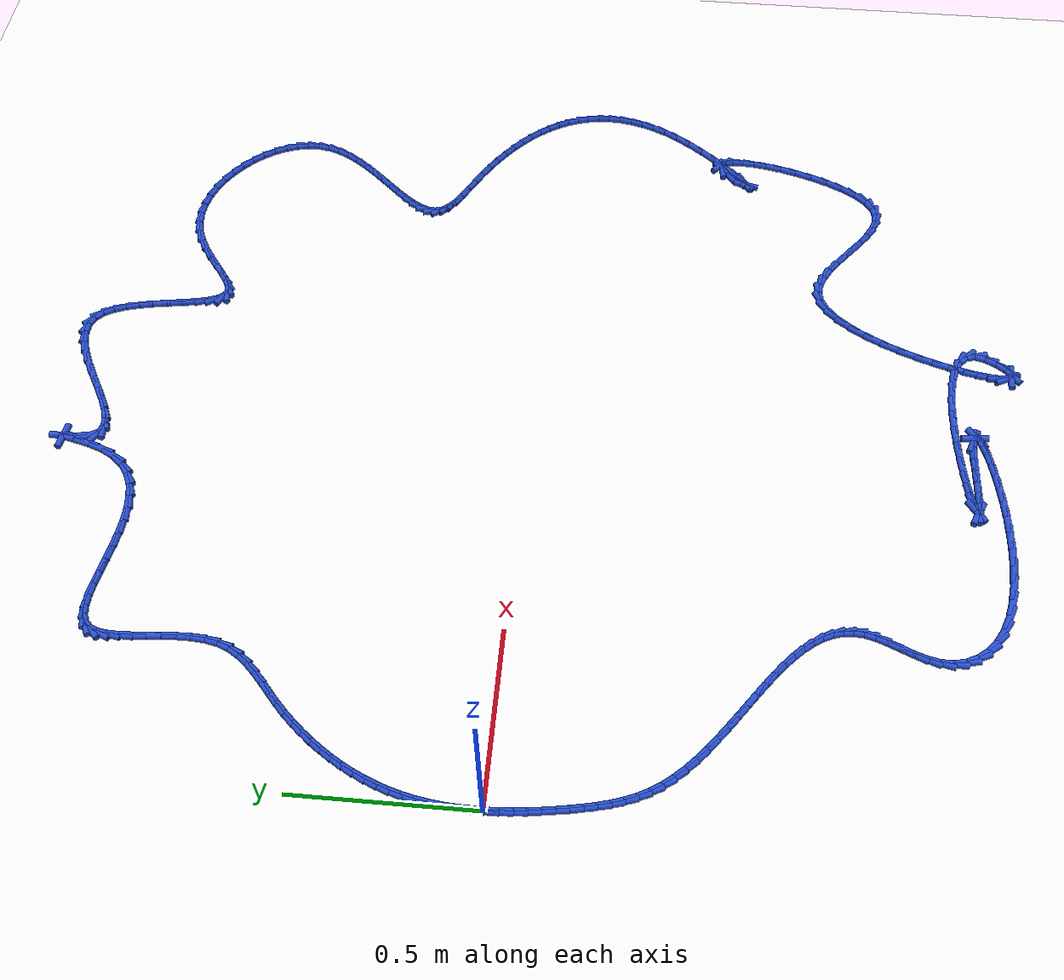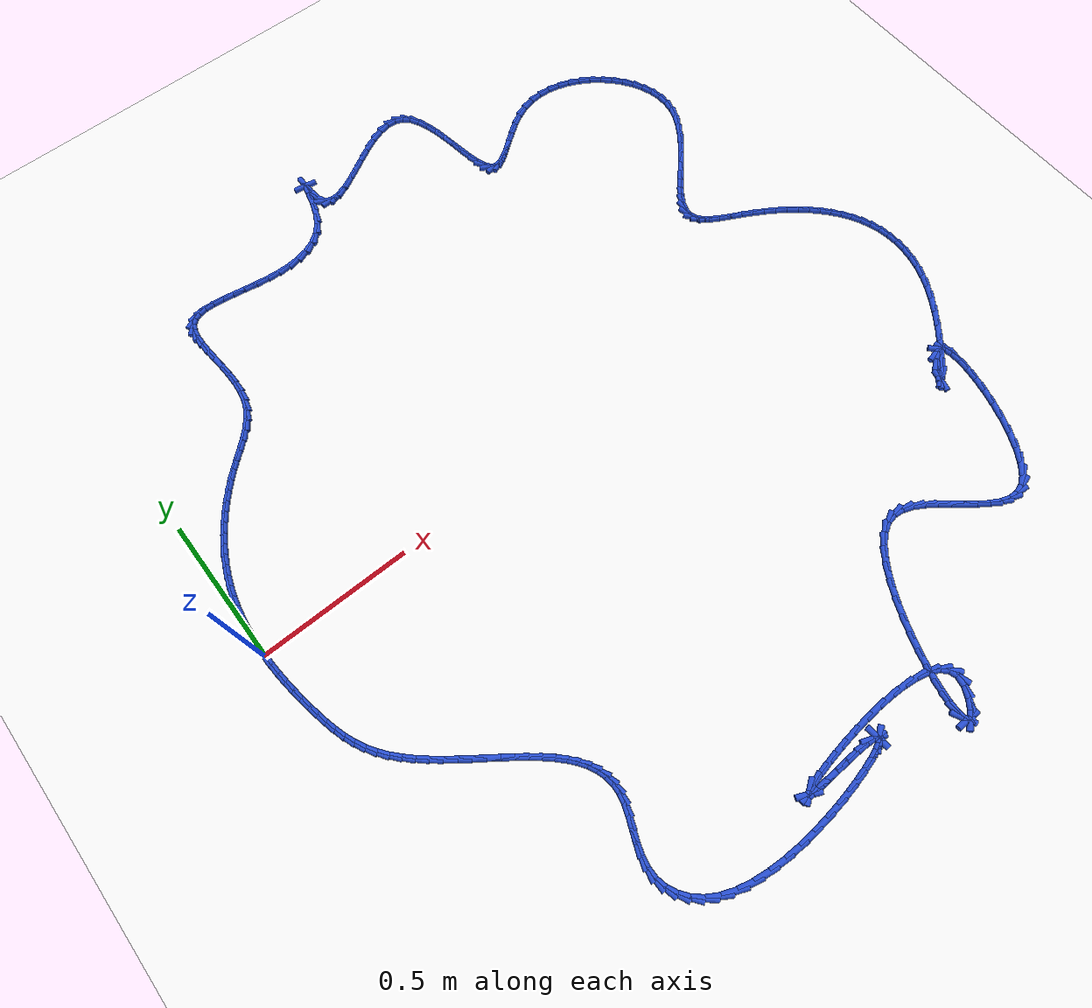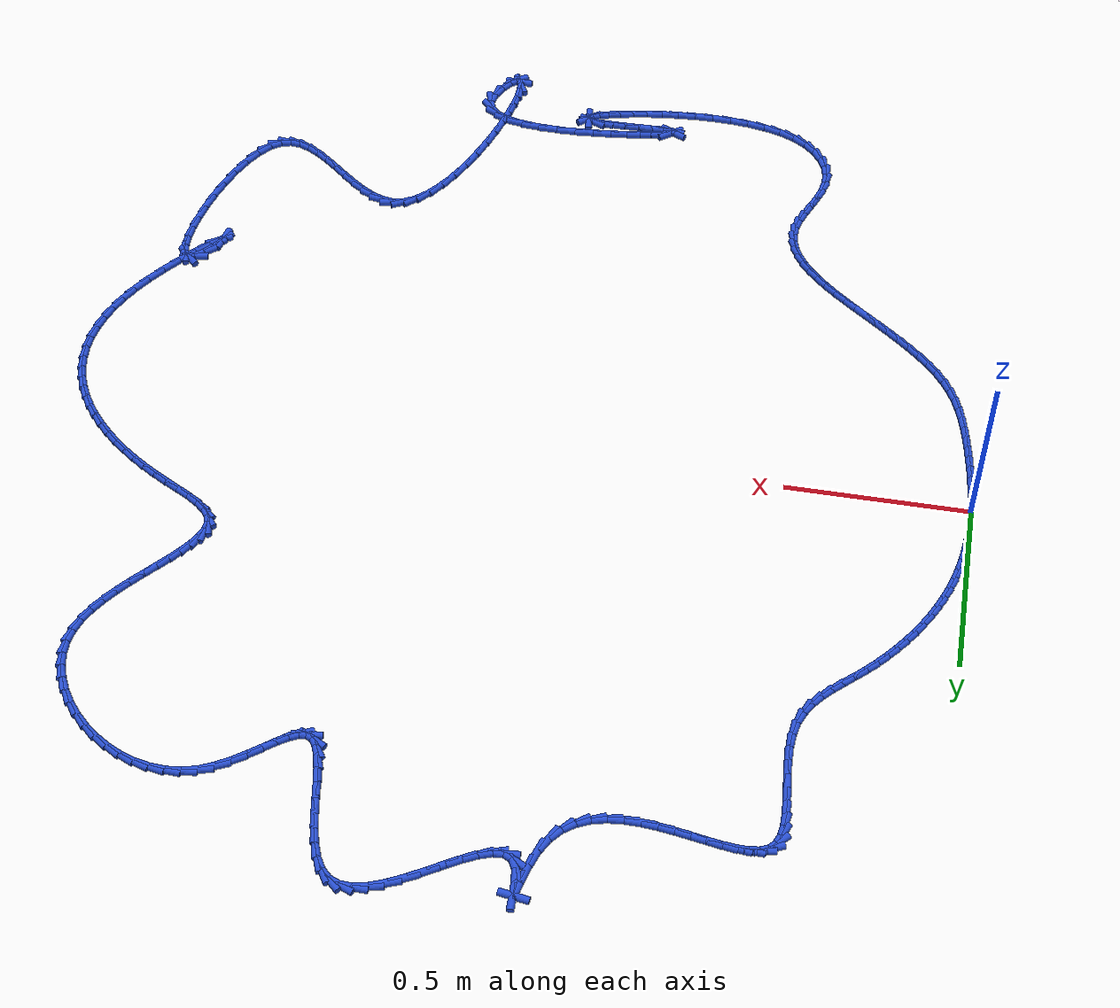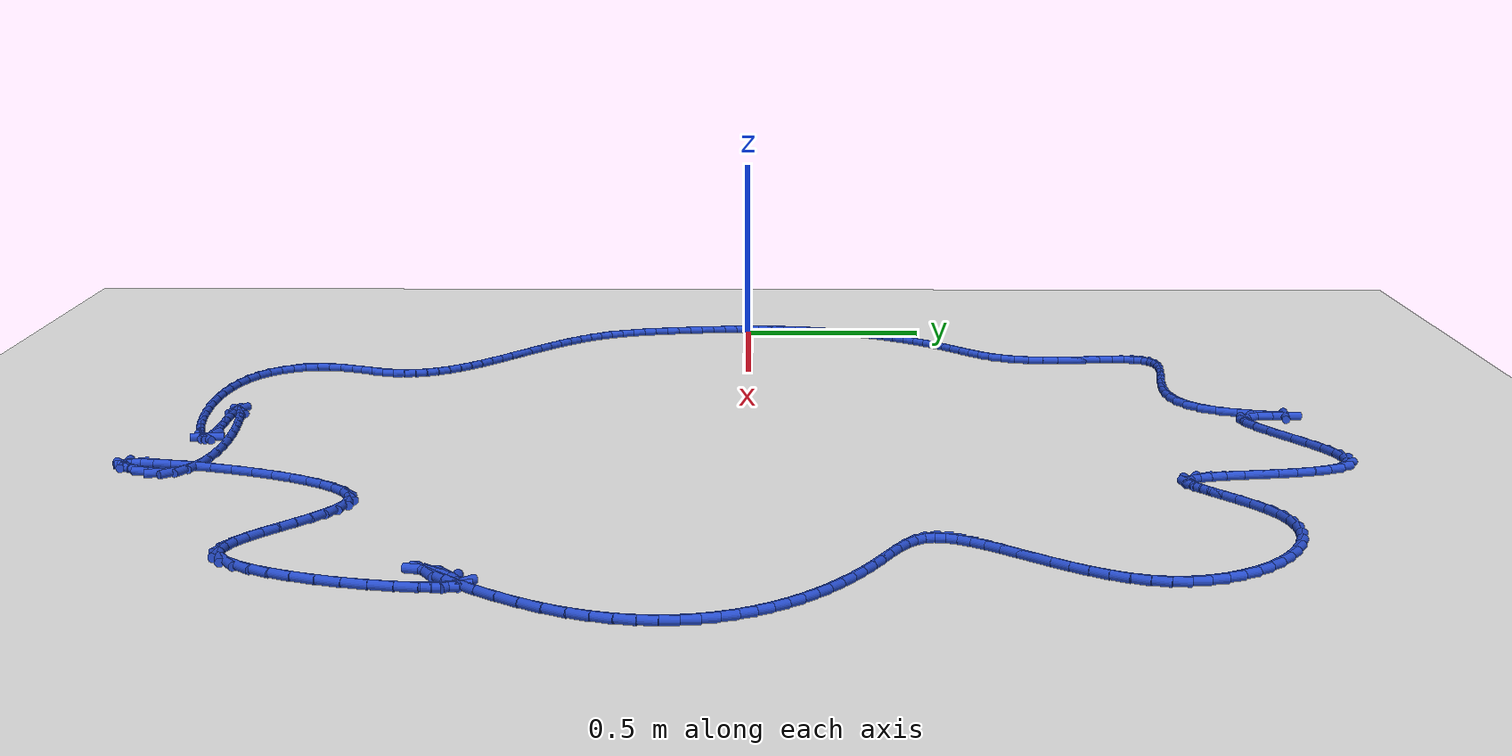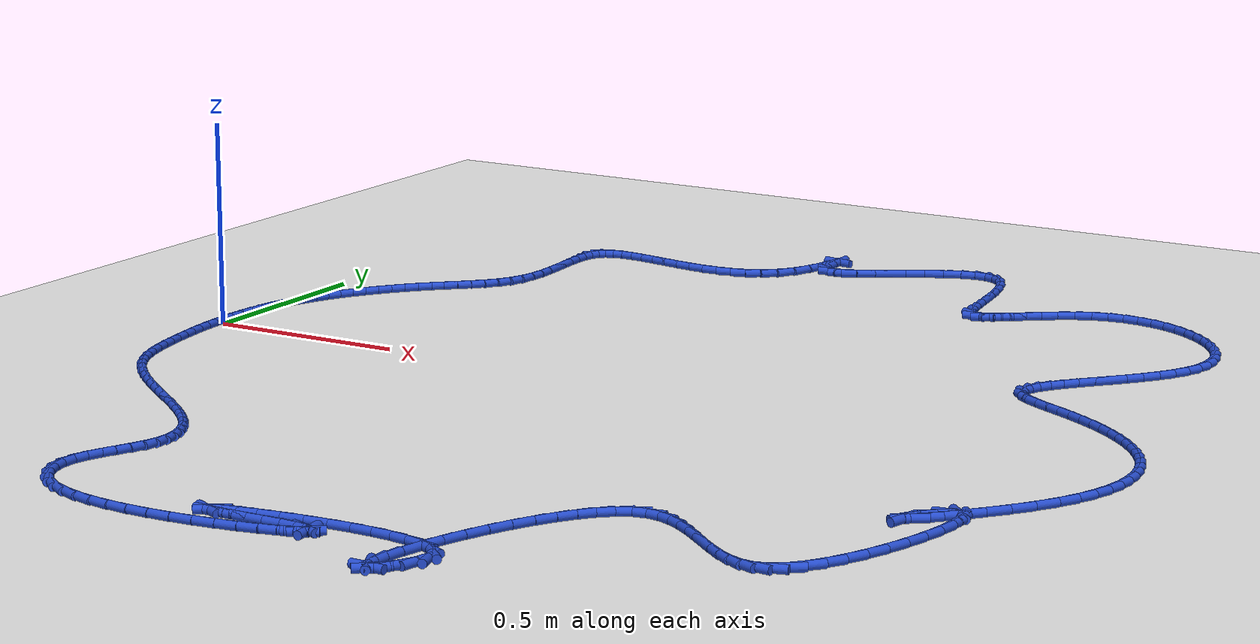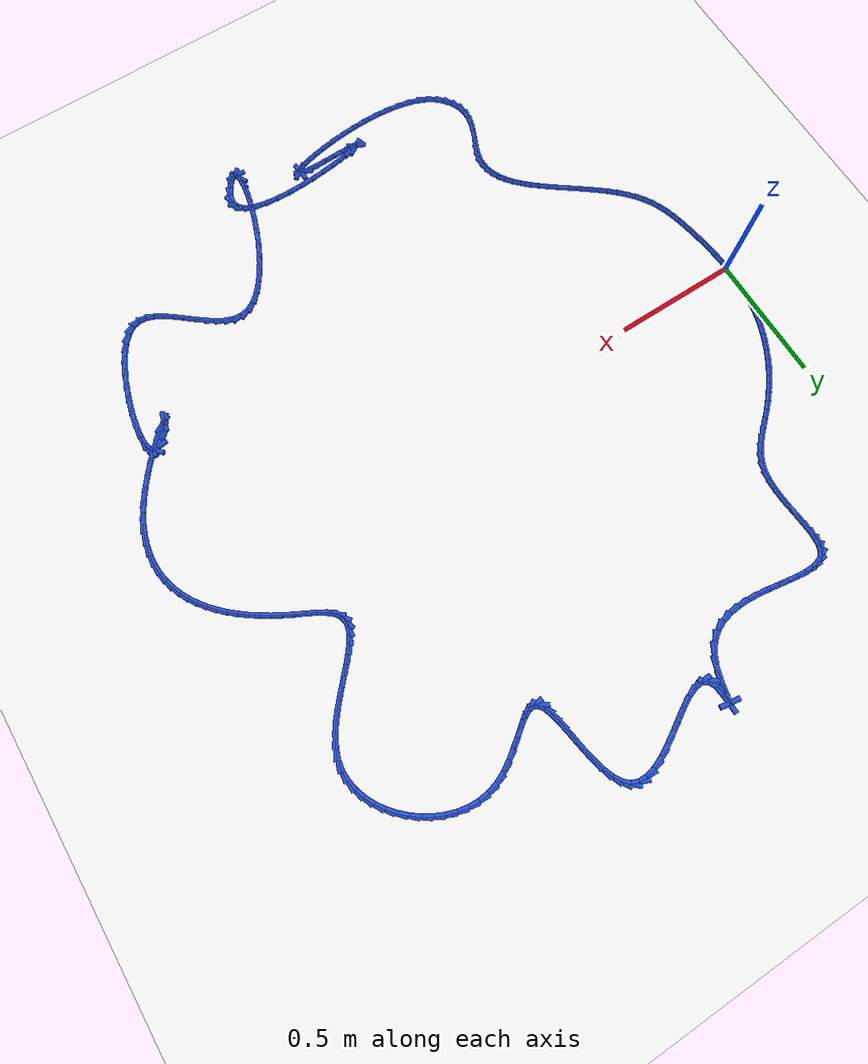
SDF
<sdf version="1.6">
 <world name="default">
  <light name="sun" type="directional">
   <pose>0 0 10 0 -0 0</pose>
   <diffuse>0.8 0.8 0.8 1</diffuse>
   <specular>0.2 0.2 0.2 1</specular>
   <attenuation>
    <range>1000</range>
    <constant>0.9</constant>
    <linear>0.01</linear>
    <quadratic>0.001</quadratic>
   </attenuation>
   <direction>-0.5 0.1 -0.9</direction>
  </light>
  <model name="ground_plane">
   <static>1</static>
   <link name="link">
    <collision name="collision">
     <geometry><plane><normal>0 0 1</normal><size>100 100</size></plane></geometry>
     <surface><friction><ode><mu>100</mu><mu2>50</mu2></ode></friction></surface>
    </collision>
    <visual name="visual">
     <cast_shadows>0</cast_shadows>
     <geometry><plane><normal>0 0 1</normal><size>100 100</size></plane></geometry>
     <material>
      <script><uri>file://media/materials/scripts/gazebo.material</uri><name>Gazebo/WhiteGlow</name></script>
     </material>
    </visual>
   </link>
  </model>
  <gravity>0 0 -9.8</gravity>
  <magnetic_field>6e-06 2.3e-05 -4.2e-05</magnetic_field>
  <atmosphere type="adiabatic"/>
  <physics name="default_physics" default="0" type="ode">
   <max_step_size>0.001</max_step_size>
   <real_time_factor>1</real_time_factor>
   <real_time_update_rate>1000</real_time_update_rate>
  </physics>
  <scene><ambient>0.4 0.4 0.4 1</ambient><background>0.7 0.7 0.7 1</background><shadows>1</shadows></scene>
  <spherical_coordinates>
   <surface_model>EARTH_WGS84</surface_model>
   <latitude_deg>0</latitude_deg>
   <longitude_deg>0</longitude_deg>
   <elevation>0</elevation>
   <heading_deg>0</heading_deg>
  </spherical_coordinates>
  <model name="line">
   <link name="link_0">
    <pose>-8.673617379884035e-19 2.0816681711721685e-17 0.01 0 1.57 -1.569305011029493</pose>
    <collision name="collision">
     <geometry><cylinder><radius>0.01</radius><length>0.08</length></cylinder></geometry>
    </collision>
    <visual name="visual">
     <material>
      <script><name>Gazebo/Blue</name><uri>file://media/materials/scripts/gazebo.material</uri></script>
     </material>
     <geometry><cylinder><radius>0.01</radius><length>0.08</length></cylinder></geometry>
    </visual>
   </link>
   <link name="link_1">
    <pose>-5.165638425430541e-05 0.03463810090234843 0.01 0 1.57 1.535135308281151</pose>
    <collision name="collision">
     <geometry><cylinder><radius>0.01</radius><length>0.08</length></cylinder></geometry>
    </collision>
    <visual name="visual">
     <material>
      <script><name>Gazebo/Blue</name><uri>file://media/materials/scripts/gazebo.material</uri></script>
     </material>
     <geometry><cylinder><radius>0.01</radius><length>0.08</length></cylinder></geometry>
    </visual>
   </link>
   <link name="link_2">
    <pose>0.001184699253228354 0.06929307010959967 0.01 0 1.57 1.4949237692335338</pose>
    <collision name="collision">
     <geometry><cylinder><radius>0.01</radius><length>0.08</length></cylinder></geometry>
    </collision>
    <visual name="visual">
     <material>
      <script><name>Gazebo/Blue</name><uri>file://media/materials/scripts/gazebo.material</uri></script>
     </material>
     <geometry><cylinder><radius>0.01</radius><length>0.08</length></cylinder></geometry>
    </visual>
   </link>
   <link name="link_3">
    <pose>0.0038124446649180884 0.10386026050504642 0.01 0 1.57 1.4514379151245504</pose>
    <collision name="collision">
     <geometry><cylinder><radius>0.01</radius><length>0.08</length></cylinder></geometry>
    </collision>
    <visual name="visual">
     <material>
      <script><name>Gazebo/Blue</name><uri>file://media/materials/scripts/gazebo.material</uri></script>
     </material>
     <geometry><cylinder><radius>0.01</radius><length>0.08</length></cylinder></geometry>
    </visual>
   </link>
   <link name="link_4">
    <pose>0.00793495760328501 0.13823502497198148 0.01 0 1.57 1.4044760355454056</pose>
    <collision name="collision">
     <geometry><cylinder><radius>0.01</radius><length>0.08</length></cylinder></geometry>
    </collision>
    <visual name="visual">
     <material>
      <script><name>Gazebo/Blue</name><uri>file://media/materials/scripts/gazebo.material</uri></script>
     </material>
     <geometry><cylinder><radius>0.01</radius><length>0.08</length></cylinder></geometry>
    </visual>
   </link>
   <link name="link_5">
    <pose>0.013655615820799228 0.17231271639369744 0.01 0 1.57 1.3538645998554175</pose>
    <collision name="collision">
     <geometry><cylinder><radius>0.01</radius><length>0.08</length></cylinder></geometry>
    </collision>
    <visual name="visual">
     <material>
      <script><name>Gazebo/Blue</name><uri>file://media/materials/scripts/gazebo.material</uri></script>
     </material>
     <geometry><cylinder><radius>0.01</radius><length>0.08</length></cylinder></geometry>
    </visual>
   </link>
   <link name="link_6">
    <pose>0.02107779706993085 0.2059886876534871 0.01 0 1.57 1.299825069877544</pose>
    <collision name="collision">
     <geometry><cylinder><radius>0.01</radius><length>0.08</length></cylinder></geometry>
    </collision>
    <visual name="visual">
     <material>
      <script><name>Gazebo/Blue</name><uri>file://media/materials/scripts/gazebo.material</uri></script>
     </material>
     <geometry><cylinder><radius>0.01</radius><length>0.08</length></cylinder></geometry>
    </visual>
   </link>
   <link name="link_7">
    <pose>0.03029375550164529 0.2391629982604923 0.01 0 1.57 1.2455566045314033</pose>
    <collision name="collision">
     <geometry><cylinder><radius>0.01</radius><length>0.08</length></cylinder></geometry>
    </collision>
    <visual name="visual">
     <material>
      <script><name>Gazebo/Blue</name><uri>file://media/materials/scripts/gazebo.material</uri></script>
     </material>
     <geometry><cylinder><radius>0.01</radius><length>0.08</length></cylinder></geometry>
    </visual>
   </link>
   <link name="link_8">
    <pose>0.041292485809758965 0.27177939893573383 0.01 0 1.57 1.1928743153756909</pose>
    <collision name="collision">
     <geometry><cylinder><radius>0.01</radius><length>0.08</length></cylinder></geometry>
    </collision>
    <visual name="visual">
     <material>
      <script><name>Gazebo/Blue</name><uri>file://media/materials/scripts/gazebo.material</uri></script>
     </material>
     <geometry><cylinder><radius>0.01</radius><length>0.08</length></cylinder></geometry>
    </visual>
   </link>
   <link name="link_9">
    <pose>0.054006954551075646 0.3038053470637475 0.01 0 1.57 1.1418372290191672</pose>
    <collision name="collision">
     <geometry><cylinder><radius>0.01</radius><length>0.08</length></cylinder></geometry>
    </collision>
    <visual name="visual">
     <material>
      <script><name>Gazebo/Blue</name><uri>file://media/materials/scripts/gazebo.material</uri></script>
     </material>
     <geometry><cylinder><radius>0.01</radius><length>0.08</length></cylinder></geometry>
    </visual>
   </link>
   <link name="link_10">
    <pose>0.06836957270695226 0.3352085351045307 0.01 0 1.57 1.0924513615860467</pose>
    <collision name="collision">
     <geometry><cylinder><radius>0.01</radius><length>0.08</length></cylinder></geometry>
    </collision>
    <visual name="visual">
     <material>
      <script><name>Gazebo/Blue</name><uri>file://media/materials/scripts/gazebo.material</uri></script>
     </material>
     <geometry><cylinder><radius>0.01</radius><length>0.08</length></cylinder></geometry>
    </visual>
   </link>
   <link name="link_11">
    <pose>0.08431275125874577 0.36595665551808104 0.01 0 1.57 1.0446920026521926</pose>
    <collision name="collision">
     <geometry><cylinder><radius>0.01</radius><length>0.08</length></cylinder></geometry>
    </collision>
    <visual name="visual">
     <material>
      <script><name>Gazebo/Blue</name><uri>file://media/materials/scripts/gazebo.material</uri></script>
     </material>
     <geometry><cylinder><radius>0.01</radius><length>0.08</length></cylinder></geometry>
    </visual>
   </link>
   <link name="link_12">
    <pose>0.10176890118781307 0.3960174007643959 0.01 0 1.57 0.9985087698773133</pose>
    <collision name="collision">
     <geometry><cylinder><radius>0.01</radius><length>0.08</length></cylinder></geometry>
    </collision>
    <visual name="visual">
     <material>
      <script><name>Gazebo/Blue</name><uri>file://media/materials/scripts/gazebo.material</uri></script>
     </material>
     <geometry><cylinder><radius>0.01</radius><length>0.08</length></cylinder></geometry>
    </visual>
   </link>
   <link name="link_13">
    <pose>0.12067043347551111 0.4253584633034729 0.01 0 1.57 0.9538304640090942</pose>
    <collision name="collision">
     <geometry><cylinder><radius>0.01</radius><length>0.08</length></cylinder></geometry>
    </collision>
    <visual name="visual">
     <material>
      <script><name>Gazebo/Blue</name><uri>file://media/materials/scripts/gazebo.material</uri></script>
     </material>
     <geometry><cylinder><radius>0.01</radius><length>0.08</length></cylinder></geometry>
    </visual>
   </link>
   <link name="link_14">
    <pose>0.1409497591031969 0.45394753559530965 0.01 0 1.57 0.9105694924464799</pose>
    <collision name="collision">
     <geometry><cylinder><radius>0.01</radius><length>0.08</length></cylinder></geometry>
    </collision>
    <visual name="visual">
     <material>
      <script><name>Gazebo/Blue</name><uri>file://media/materials/scripts/gazebo.material</uri></script>
     </material>
     <geometry><cylinder><radius>0.01</radius><length>0.08</length></cylinder></geometry>
    </visual>
   </link>
   <link name="link_15">
    <pose>0.16253928905222723 0.48175231009990327 0.01 0 1.57 0.868625728667463</pose>
    <collision name="collision">
     <geometry><cylinder><radius>0.01</radius><length>0.08</length></cylinder></geometry>
    </collision>
    <visual name="visual">
     <material>
      <script><name>Gazebo/Blue</name><uri>file://media/materials/scripts/gazebo.material</uri></script>
     </material>
     <geometry><cylinder><radius>0.01</radius><length>0.08</length></cylinder></geometry>
    </visual>
   </link>
   <link name="link_16">
    <pose>0.18537143430395914 0.5087404792772516 0.01 0 1.57 0.8278897530611945</pose>
    <collision name="collision">
     <geometry><cylinder><radius>0.01</radius><length>0.08</length></cylinder></geometry>
    </collision>
    <visual name="visual">
     <material>
      <script><name>Gazebo/Blue</name><uri>file://media/materials/scripts/gazebo.material</uri></script>
     </material>
     <geometry><cylinder><radius>0.01</radius><length>0.08</length></cylinder></geometry>
    </visual>
   </link>
   <link name="link_17">
    <pose>0.2093786058397495 0.534879735587352 0.01 0 1.57 0.7882454769520455</pose>
    <collision name="collision">
     <geometry><cylinder><radius>0.01</radius><length>0.08</length></cylinder></geometry>
    </collision>
    <visual name="visual">
     <material>
      <script><name>Gazebo/Blue</name><uri>file://media/materials/scripts/gazebo.material</uri></script>
     </material>
     <geometry><cylinder><radius>0.01</radius><length>0.08</length></cylinder></geometry>
    </visual>
   </link>
   <link name="link_18">
    <pose>0.2344932146409553 0.5601377714902019 0.01 0 1.57 0.7511786405013481</pose>
    <collision name="collision">
     <geometry><cylinder><radius>0.01</radius><length>0.08</length></cylinder></geometry>
    </collision>
    <visual name="visual">
     <material>
      <script><name>Gazebo/Blue</name><uri>file://media/materials/scripts/gazebo.material</uri></script>
     </material>
     <geometry><cylinder><radius>0.01</radius><length>0.08</length></cylinder></geometry>
    </visual>
   </link>
   <link name="link_19">
    <pose>0.2606018262244585 0.584518004226917 0.01 0 1.57 0.7355004092096742</pose>
    <collision name="collision">
     <geometry><cylinder><radius>0.01</radius><length>0.08</length></cylinder></geometry>
    </collision>
    <visual name="visual">
     <material>
      <script><name>Gazebo/Blue</name><uri>file://media/materials/scripts/gazebo.material</uri></script>
     </material>
     <geometry><cylinder><radius>0.01</radius><length>0.08</length></cylinder></geometry>
    </visual>
   </link>
   <link name="link_20">
    <pose>0.28704715299012945 0.608447645055929 0.01 0 1.57 0.7536811572723947</pose>
    <collision name="collision">
     <geometry><cylinder><radius>0.01</radius><length>0.08</length></cylinder></geometry>
    </collision>
    <visual name="visual">
     <material>
      <script><name>Gazebo/Blue</name><uri>file://media/materials/scripts/gazebo.material</uri></script>
     </material>
     <geometry><cylinder><radius>0.01</radius><length>0.08</length></cylinder></geometry>
    </visual>
   </link>
   <link name="link_21">
    <pose>0.31281578849473135 0.6326314085365454 0.01 0 1.57 0.8072365346144506</pose>
    <collision name="collision">
     <geometry><cylinder><radius>0.01</radius><length>0.08</length></cylinder></geometry>
    </collision>
    <visual name="visual">
     <material>
      <script><name>Gazebo/Blue</name><uri>file://media/materials/scripts/gazebo.material</uri></script>
     </material>
     <geometry><cylinder><radius>0.01</radius><length>0.08</length></cylinder></geometry>
    </visual>
   </link>
   <link name="link_22">
    <pose>0.3368881507835388 0.6577788214553848 0.01 0 1.57 0.8983321688613249</pose>
    <collision name="collision">
     <geometry><cylinder><radius>0.01</radius><length>0.08</length></cylinder></geometry>
    </collision>
    <visual name="visual">
     <material>
      <script><name>Gazebo/Blue</name><uri>file://media/materials/scripts/gazebo.material</uri></script>
     </material>
     <geometry><cylinder><radius>0.01</radius><length>0.08</length></cylinder></geometry>
    </visual>
   </link>
   <link name="link_23">
    <pose>0.3582446579018264 0.6845994105990653 0.01 0 1.57 1.0278855086694925</pose>
    <collision name="collision">
     <geometry><cylinder><radius>0.01</radius><length>0.08</length></cylinder></geometry>
    </collision>
    <visual name="visual">
     <material>
      <script><name>Gazebo/Blue</name><uri>file://media/materials/scripts/gazebo.material</uri></script>
     </material>
     <geometry><cylinder><radius>0.01</radius><length>0.08</length></cylinder></geometry>
    </visual>
   </link>
   <link name="link_24">
    <pose>0.3758657278948691 0.7138027027542058 0.01 0 1.57 1.191670472003382</pose>
    <collision name="collision">
     <geometry><cylinder><radius>0.01</radius><length>0.08</length></cylinder></geometry>
    </collision>
    <visual name="visual">
     <material>
      <script><name>Gazebo/Blue</name><uri>file://media/materials/scripts/gazebo.material</uri></script>
     </material>
     <geometry><cylinder><radius>0.01</radius><length>0.08</length></cylinder></geometry>
    </visual>
   </link>
   <link name="link_25">
    <pose>0.38873213377500665 0.7460979406390422 0.01 0 1.57 1.3618860238097712</pose>
    <collision name="collision">
     <geometry><cylinder><radius>0.01</radius><length>0.08</length></cylinder></geometry>
    </collision>
    <visual name="visual">
     <material>
      <script><name>Gazebo/Blue</name><uri>file://media/materials/scripts/gazebo.material</uri></script>
     </material>
     <geometry><cylinder><radius>0.01</radius><length>0.08</length></cylinder></geometry>
    </visual>
   </link>
   <link name="link_26">
    <pose>0.3963034667434989 0.7818111846388585 0.01 0 1.57 1.4884840408029265</pose>
    <collision name="collision">
     <geometry><cylinder><radius>0.01</radius><length>0.08</length></cylinder></geometry>
    </collision>
    <visual name="visual">
     <material>
      <script><name>Gazebo/Blue</name><uri>file://media/materials/scripts/gazebo.material</uri></script>
     </material>
     <geometry><cylinder><radius>0.01</radius><length>0.08</length></cylinder></geometry>
    </visual>
   </link>
   <link name="link_27">
    <pose>0.3994645480395753 0.8201279307585918 0.01 0 1.57 -1.568280550347962</pose>
    <collision name="collision">
     <geometry><cylinder><radius>0.01</radius><length>0.08</length></cylinder></geometry>
    </collision>
    <visual name="visual">
     <material>
      <script><name>Gazebo/Blue</name><uri>file://media/materials/scripts/gazebo.material</uri></script>
     </material>
     <geometry><cylinder><radius>0.01</radius><length>0.08</length></cylinder></geometry>
    </visual>
   </link>
   <link name="link_28">
    <pose>0.39936418221671255 0.860022417902772 0.01 0 1.57 -1.5161363240205563</pose>
    <collision name="collision">
     <geometry><cylinder><radius>0.01</radius><length>0.08</length></cylinder></geometry>
    </collision>
    <visual name="visual">
     <material>
      <script><name>Gazebo/Blue</name><uri>file://media/materials/scripts/gazebo.material</uri></script>
     </material>
     <geometry><cylinder><radius>0.01</radius><length>0.08</length></cylinder></geometry>
    </visual>
   </link>
   <link name="link_29">
    <pose>0.3971511738283869 0.9004688849759277 0.01 0 1.57 -1.4914875968822228</pose>
    <collision name="collision">
     <geometry><cylinder><radius>0.01</radius><length>0.08</length></cylinder></geometry>
    </collision>
    <visual name="visual">
     <material>
      <script><name>Gazebo/Blue</name><uri>file://media/materials/scripts/gazebo.material</uri></script>
     </material>
     <geometry><cylinder><radius>0.01</radius><length>0.08</length></cylinder></geometry>
    </visual>
   </link>
   <link name="link_30">
    <pose>0.39397432742807487 0.9404415708825893 0.01 0 1.57 -1.4931871096889804</pose>
    <collision name="collision">
     <geometry><cylinder><radius>0.01</radius><length>0.08</length></cylinder></geometry>
    </collision>
    <visual name="visual">
     <material>
      <script><name>Gazebo/Blue</name><uri>file://media/materials/scripts/gazebo.material</uri></script>
     </material>
     <geometry><cylinder><radius>0.01</radius><length>0.08</length></cylinder></geometry>
    </visual>
   </link>
   <link name="link_31">
    <pose>0.390982447569253 0.9789147145272856 0.01 0 1.57 -1.5247035895243215</pose>
    <collision name="collision">
     <geometry><cylinder><radius>0.01</radius><length>0.08</length></cylinder></geometry>
    </collision>
    <visual name="visual">
     <material>
      <script><name>Gazebo/Blue</name><uri>file://media/materials/scripts/gazebo.material</uri></script>
     </material>
     <geometry><cylinder><radius>0.01</radius><length>0.08</length></cylinder></geometry>
    </visual>
   </link>
   <link name="link_32">
    <pose>0.3893243388053978 1.0148625548145471 0.01 0 1.57 1.5453527774657991</pose>
    <collision name="collision">
     <geometry><cylinder><radius>0.01</radius><length>0.08</length></cylinder></geometry>
    </collision>
    <visual name="visual">
     <material>
      <script><name>Gazebo/Blue</name><uri>file://media/materials/scripts/gazebo.material</uri></script>
     </material>
     <geometry><cylinder><radius>0.01</radius><length>0.08</length></cylinder></geometry>
    </visual>
   </link>
   <link name="link_33">
    <pose>0.3901488056899858 1.0472593306489026 0.01 0 1.57 1.411977918099629</pose>
    <collision name="collision">
     <geometry><cylinder><radius>0.01</radius><length>0.08</length></cylinder></geometry>
    </collision>
    <visual name="visual">
     <material>
      <script><name>Gazebo/Blue</name><uri>file://media/materials/scripts/gazebo.material</uri></script>
     </material>
     <geometry><cylinder><radius>0.01</radius><length>0.08</length></cylinder></geometry>
    </visual>
   </link>
   <link name="link_34">
    <pose>0.39460465277649315 1.075079280934882 0.01 0 1.57 1.1768186514291217</pose>
    <collision name="collision">
     <geometry><cylinder><radius>0.01</radius><length>0.08</length></cylinder></geometry>
    </collision>
    <visual name="visual">
     <material>
      <script><name>Gazebo/Blue</name><uri>file://media/materials/scripts/gazebo.material</uri></script>
     </material>
     <geometry><cylinder><radius>0.01</radius><length>0.08</length></cylinder></geometry>
    </visual>
   </link>
   <link name="link_35">
    <pose>0.40384068461839656 1.0972966445770143 0.01 0 1.57 0.8036534141712126</pose>
    <collision name="collision">
     <geometry><cylinder><radius>0.01</radius><length>0.08</length></cylinder></geometry>
    </collision>
    <visual name="visual">
     <material>
      <script><name>Gazebo/Blue</name><uri>file://media/materials/scripts/gazebo.material</uri></script>
     </material>
     <geometry><cylinder><radius>0.01</radius><length>0.08</length></cylinder></geometry>
    </visual>
   </link>
   <link name="link_36">
    <pose>0.4189405103541768 1.112958087372414 0.01 0 1.57 0.4150669243652497</pose>
    <collision name="collision">
     <geometry><cylinder><radius>0.01</radius><length>0.08</length></cylinder></geometry>
    </collision>
    <visual name="visual">
     <material>
      <script><name>Gazebo/Blue</name><uri>file://media/materials/scripts/gazebo.material</uri></script>
     </material>
     <geometry><cylinder><radius>0.01</radius><length>0.08</length></cylinder></geometry>
    </visual>
   </link>
   <link name="link_37">
    <pose>0.4399801688791699 1.1222296050860623 0.01 0 1.57 0.14845639626658577</pose>
    <collision name="collision">
     <geometry><cylinder><radius>0.01</radius><length>0.08</length></cylinder></geometry>
    </collision>
    <visual name="visual">
     <material>
      <script><name>Gazebo/Blue</name><uri>file://media/materials/scripts/gazebo.material</uri></script>
     </material>
     <geometry><cylinder><radius>0.01</radius><length>0.08</length></cylinder></geometry>
    </visual>
   </link>
   <link name="link_38">
    <pose>0.4662433417337023 1.126157439141993 0.01 0 1.57 -0.011247543446740244</pose>
    <collision name="collision">
     <geometry><cylinder><radius>0.01</radius><length>0.08</length></cylinder></geometry>
    </collision>
    <visual name="visual">
     <material>
      <script><name>Gazebo/Blue</name><uri>file://media/materials/scripts/gazebo.material</uri></script>
     </material>
     <geometry><cylinder><radius>0.01</radius><length>0.08</length></cylinder></geometry>
    </visual>
   </link>
   <link name="link_39">
    <pose>0.4969923381550465 1.1258115738838583 0.01 0 1.57 -0.1025341059133014</pose>
    <collision name="collision">
     <geometry><cylinder><radius>0.01</radius><length>0.08</length></cylinder></geometry>
    </collision>
    <visual name="visual">
     <material>
      <script><name>Gazebo/Blue</name><uri>file://media/materials/scripts/gazebo.material</uri></script>
     </material>
     <geometry><cylinder><radius>0.01</radius><length>0.08</length></cylinder></geometry>
    </visual>
   </link>
   <link name="link_40">
    <pose>0.531489467380474 1.1222619936553102 0.01 0 1.57 -0.15038043305676224</pose>
    <collision name="collision">
     <geometry><cylinder><radius>0.01</radius><length>0.08</length></cylinder></geometry>
    </collision>
    <visual name="visual">
     <material>
      <script><name>Gazebo/Blue</name><uri>file://media/materials/scripts/gazebo.material</uri></script>
     </material>
     <geometry><cylinder><radius>0.01</radius><length>0.08</length></cylinder></geometry>
    </visual>
   </link>
   <link name="link_41">
    <pose>0.5689970386472569 1.1165786828 0.01 0 1.57 -0.16800905003659292</pose>
    <collision name="collision">
     <geometry><cylinder><radius>0.01</radius><length>0.08</length></cylinder></geometry>
    </collision>
    <visual name="visual">
     <material>
      <script><name>Gazebo/Blue</name><uri>file://media/materials/scripts/gazebo.material</uri></script>
     </material>
     <geometry><cylinder><radius>0.01</radius><length>0.08</length></cylinder></geometry>
    </visual>
   </link>
   <link name="link_42">
    <pose>0.6087773611926669 1.10983162566158 0.01 0 1.57 -0.161730169987351</pose>
    <collision name="collision">
     <geometry><cylinder><radius>0.01</radius><length>0.08</length></cylinder></geometry>
    </collision>
    <visual name="visual">
     <material>
      <script><name>Gazebo/Blue</name><uri>file://media/materials/scripts/gazebo.material</uri></script>
     </material>
     <geometry><cylinder><radius>0.01</radius><length>0.08</length></cylinder></geometry>
    </visual>
   </link>
   <link name="link_43">
    <pose>0.6500927442539758 1.1030908065837022 0.01 0 1.57 -0.1337077071958004</pose>
    <collision name="collision">
     <geometry><cylinder><radius>0.01</radius><length>0.08</length></cylinder></geometry>
    </collision>
    <visual name="visual">
     <material>
      <script><name>Gazebo/Blue</name><uri>file://media/materials/scripts/gazebo.material</uri></script>
     </material>
     <geometry><cylinder><radius>0.01</radius><length>0.08</length></cylinder></geometry>
    </visual>
   </link>
   <link name="link_44">
    <pose>0.6922054970684561 1.0974262099100183 0.01 0 1.57 -0.08323591101266663</pose>
    <collision name="collision">
     <geometry><cylinder><radius>0.01</radius><length>0.08</length></cylinder></geometry>
    </collision>
    <visual name="visual">
     <material>
      <script><name>Gazebo/Blue</name><uri>file://media/materials/scripts/gazebo.material</uri></script>
     </material>
     <geometry><cylinder><radius>0.01</radius><length>0.08</length></cylinder></geometry>
    </visual>
   </link>
   <link name="link_45">
    <pose>0.7343779288733792 1.0939078199841799 0.01 0 1.57 -0.007282750099045498</pose>
    <collision name="collision">
     <geometry><cylinder><radius>0.01</radius><length>0.08</length></cylinder></geometry>
    </collision>
    <visual name="visual">
     <material>
      <script><name>Gazebo/Blue</name><uri>file://media/materials/scripts/gazebo.material</uri></script>
     </material>
     <geometry><cylinder><radius>0.01</radius><length>0.08</length></cylinder></geometry>
    </visual>
   </link>
   <link name="link_46">
    <pose>0.7758723489060166 1.0936056211498393 0.01 0 1.57 0.09907831530717444</pose>
    <collision name="collision">
     <geometry><cylinder><radius>0.01</radius><length>0.08</length></cylinder></geometry>
    </collision>
    <visual name="visual">
     <material>
      <script><name>Gazebo/Blue</name><uri>file://media/materials/scripts/gazebo.material</uri></script>
     </material>
     <geometry><cylinder><radius>0.01</radius><length>0.08</length></cylinder></geometry>
    </visual>
   </link>
   <link name="link_47">
    <pose>0.8159510664036412 1.0975895977506478 0.01 0 1.57 0.24147163791698817</pose>
    <collision name="collision">
     <geometry><cylinder><radius>0.01</radius><length>0.08</length></cylinder></geometry>
    </collision>
    <visual name="visual">
     <material>
      <script><name>Gazebo/Blue</name><uri>file://media/materials/scripts/gazebo.material</uri></script>
     </material>
     <geometry><cylinder><radius>0.01</radius><length>0.08</length></cylinder></geometry>
    </visual>
   </link>
   <link name="link_48">
    <pose>0.8538763906035245 1.106929734130258 0.01 0 1.57 0.4228746348597719</pose>
    <collision name="collision">
     <geometry><cylinder><radius>0.01</radius><length>0.08</length></cylinder></geometry>
    </collision>
    <visual name="visual">
     <material>
      <script><name>Gazebo/Blue</name><uri>file://media/materials/scripts/gazebo.material</uri></script>
     </material>
     <geometry><cylinder><radius>0.01</radius><length>0.08</length></cylinder></geometry>
    </visual>
   </link>
   <link name="link_49">
    <pose>0.8889106307429382 1.1226960146323213 0.01 0 1.57 0.6375303209361082</pose>
    <collision name="collision">
     <geometry><cylinder><radius>0.01</radius><length>0.08</length></cylinder></geometry>
    </collision>
    <visual name="visual">
     <material>
      <script><name>Gazebo/Blue</name><uri>file://media/materials/scripts/gazebo.material</uri></script>
     </material>
     <geometry><cylinder><radius>0.01</radius><length>0.08</length></cylinder></geometry>
    </visual>
   </link>
   <link name="link_50">
    <pose>0.9203160960591543 1.1459584236004896 0.01 0 1.57 0.8665803744971301</pose>
    <collision name="collision">
     <geometry><cylinder><radius>0.01</radius><length>0.08</length></cylinder></geometry>
    </collision>
    <visual name="visual">
     <material>
      <script><name>Gazebo/Blue</name><uri>file://media/materials/scripts/gazebo.material</uri></script>
     </material>
     <geometry><cylinder><radius>0.01</radius><length>0.08</length></cylinder></geometry>
    </visual>
   </link>
   <link name="link_51">
    <pose>0.9473550957894448 1.1777869453784149 0.01 0 1.57 1.084192181204953</pose>
    <collision name="collision">
     <geometry><cylinder><radius>0.01</radius><length>0.08</length></cylinder></geometry>
    </collision>
    <visual name="visual">
     <material>
      <script><name>Gazebo/Blue</name><uri>file://media/materials/scripts/gazebo.material</uri></script>
     </material>
     <geometry><cylinder><radius>0.01</radius><length>0.08</length></cylinder></geometry>
    </visual>
   </link>
   <link name="link_52">
    <pose>0.9692901415719178 1.2192493929146635 0.01 0 1.57 1.248725836965864</pose>
    <collision name="collision">
     <geometry><cylinder><radius>0.01</radius><length>0.08</length></cylinder></geometry>
    </collision>
    <visual name="visual">
     <material>
      <script><name>Gazebo/Blue</name><uri>file://media/materials/scripts/gazebo.material</uri></script>
     </material>
     <geometry><cylinder><radius>0.01</radius><length>0.08</length></cylinder></geometry>
    </visual>
   </link>
   <link name="link_53">
    <pose>0.9856704347898763 1.2683379164565447 0.01 0 1.57 1.3287912689701837</pose>
    <collision name="collision">
     <geometry><cylinder><radius>0.01</radius><length>0.08</length></cylinder></geometry>
    </collision>
    <visual name="visual">
     <material>
      <script><name>Gazebo/Blue</name><uri>file://media/materials/scripts/gazebo.material</uri></script>
     </material>
     <geometry><cylinder><radius>0.01</radius><length>0.08</length></cylinder></geometry>
    </visual>
   </link>
   <link name="link_54">
    <pose>0.996902928241898 1.3138425441694352 0.01 0 1.57 1.3453167303175664</pose>
    <collision name="collision">
     <geometry><cylinder><radius>0.01</radius><length>0.08</length></cylinder></geometry>
    </collision>
    <visual name="visual">
     <material>
      <script><name>Gazebo/Blue</name><uri>file://media/materials/scripts/gazebo.material</uri></script>
     </material>
     <geometry><cylinder><radius>0.01</radius><length>0.08</length></cylinder></geometry>
    </visual>
   </link>
   <link name="link_55">
    <pose>1.0035543027198472 1.3428397115997508 0.01 0 1.57 -0.1525639041829774</pose>
    <collision name="collision">
     <geometry><cylinder><radius>0.01</radius><length>0.08</length></cylinder></geometry>
    </collision>
    <visual name="visual">
     <material>
      <script><name>Gazebo/Blue</name><uri>file://media/materials/scripts/gazebo.material</uri></script>
     </material>
     <geometry><cylinder><radius>0.01</radius><length>0.08</length></cylinder></geometry>
    </visual>
   </link>
   <link name="link_56">
    <pose>1.00619513793922 1.3424336601859812 0.01 0 1.57 -1.549513623553215</pose>
    <collision name="collision">
     <geometry><cylinder><radius>0.01</radius><length>0.08</length></cylinder></geometry>
    </collision>
    <visual name="visual">
     <material>
      <script><name>Gazebo/Blue</name><uri>file://media/materials/scripts/gazebo.material</uri></script>
     </material>
     <geometry><cylinder><radius>0.01</radius><length>0.08</length></cylinder></geometry>
    </visual>
   </link>
   <link name="link_57">
    <pose>1.0068790258110933 1.3103050060140167 0.01 0 1.57 -1.4582031845294052</pose>
    <collision name="collision">
     <geometry><cylinder><radius>0.01</radius><length>0.08</length></cylinder></geometry>
    </collision>
    <visual name="visual">
     <material>
      <script><name>Gazebo/Blue</name><uri>file://media/materials/scripts/gazebo.material</uri></script>
     </material>
     <geometry><cylinder><radius>0.01</radius><length>0.08</length></cylinder></geometry>
    </visual>
   </link>
   <link name="link_58">
    <pose>1.0113692427907868 1.2705936492558776 0.01 0 1.57 -1.1039511954821721</pose>
    <collision name="collision">
     <geometry><cylinder><radius>0.01</radius><length>0.08</length></cylinder></geometry>
    </collision>
    <visual name="visual">
     <material>
      <script><name>Gazebo/Blue</name><uri>file://media/materials/scripts/gazebo.material</uri></script>
     </material>
     <geometry><cylinder><radius>0.01</radius><length>0.08</length></cylinder></geometry>
    </visual>
   </link>
   <link name="link_59">
    <pose>1.0243493915601605 1.244839555315182 0.01 0 1.57 -0.46505238405204813</pose>
    <collision name="collision">
     <geometry><cylinder><radius>0.01</radius><length>0.08</length></cylinder></geometry>
    </collision>
    <visual name="visual">
     <material>
      <script><name>Gazebo/Blue</name><uri>file://media/materials/scripts/gazebo.material</uri></script>
     </material>
     <geometry><cylinder><radius>0.01</radius><length>0.08</length></cylinder></geometry>
    </visual>
   </link>
   <link name="link_60">
    <pose>1.0454705786687613 1.2342418475220112 0.01 0 1.57 0.0676781002996856</pose>
    <collision name="collision">
     <geometry><cylinder><radius>0.01</radius><length>0.08</length></cylinder></geometry>
    </collision>
    <visual name="visual">
     <material>
      <script><name>Gazebo/Blue</name><uri>file://media/materials/scripts/gazebo.material</uri></script>
     </material>
     <geometry><cylinder><radius>0.01</radius><length>0.08</length></cylinder></geometry>
    </visual>
   </link>
   <link name="link_61">
    <pose>1.0734282244914604 1.2361368620249322 0.01 0 1.57 0.3367476848698128</pose>
    <collision name="collision">
     <geometry><cylinder><radius>0.01</radius><length>0.08</length></cylinder></geometry>
    </collision>
    <visual name="visual">
     <material>
      <script><name>Gazebo/Blue</name><uri>file://media/materials/scripts/gazebo.material</uri></script>
     </material>
     <geometry><cylinder><radius>0.01</radius><length>0.08</length></cylinder></geometry>
    </visual>
   </link>
   <link name="link_62">
    <pose>1.1069177494031317 1.2478609349725167 0.01 0 1.57 0.46430609760443864</pose>
    <collision name="collision">
     <geometry><cylinder><radius>0.01</radius><length>0.08</length></cylinder></geometry>
    </collision>
    <visual name="visual">
     <material>
      <script><name>Gazebo/Blue</name><uri>file://media/materials/scripts/gazebo.material</uri></script>
     </material>
     <geometry><cylinder><radius>0.01</radius><length>0.08</length></cylinder></geometry>
    </visual>
   </link>
   <link name="link_63">
    <pose>1.1446345737786479 1.266750402513332 0.01 0 1.57 0.522268012151314</pose>
    <collision name="collision">
     <geometry><cylinder><radius>0.01</radius><length>0.08</length></cylinder></geometry>
    </collision>
    <visual name="visual">
     <material>
      <script><name>Gazebo/Blue</name><uri>file://media/materials/scripts/gazebo.material</uri></script>
     </material>
     <geometry><cylinder><radius>0.01</radius><length>0.08</length></cylinder></geometry>
    </visual>
   </link>
   <link name="link_64">
    <pose>1.1852741179928812 1.2901416007959492 0.01 0 1.57 0.5382356035446642</pose>
    <collision name="collision">
     <geometry><cylinder><radius>0.01</radius><length>0.08</length></cylinder></geometry>
    </collision>
    <visual name="visual">
     <material>
      <script><name>Gazebo/Blue</name><uri>file://media/materials/scripts/gazebo.material</uri></script>
     </material>
     <geometry><cylinder><radius>0.01</radius><length>0.08</length></cylinder></geometry>
    </visual>
   </link>
   <link name="link_65">
    <pose>1.2275318024207047 1.3153708659689367 0.01 0 1.57 0.5205128452473726</pose>
    <collision name="collision">
     <geometry><cylinder><radius>0.01</radius><length>0.08</length></cylinder></geometry>
    </collision>
    <visual name="visual">
     <material>
      <script><name>Gazebo/Blue</name><uri>file://media/materials/scripts/gazebo.material</uri></script>
     </material>
     <geometry><cylinder><radius>0.01</radius><length>0.08</length></cylinder></geometry>
    </visual>
   </link>
   <link name="link_66">
    <pose>1.270103047436991 1.3397745341808638 0.01 0 1.57 0.46603616227903977</pose>
    <collision name="collision">
     <geometry><cylinder><radius>0.01</radius><length>0.08</length></cylinder></geometry>
    </collision>
    <visual name="visual">
     <material>
      <script><name>Gazebo/Blue</name><uri>file://media/materials/scripts/gazebo.material</uri></script>
     </material>
     <geometry><cylinder><radius>0.01</radius><length>0.08</length></cylinder></geometry>
    </visual>
   </link>
   <link name="link_67">
    <pose>1.311683273416612 1.3606889415803 0.01 0 1.57 0.3638203418146919</pose>
    <collision name="collision">
     <geometry><cylinder><radius>0.01</radius><length>0.08</length></cylinder></geometry>
    </collision>
    <visual name="visual">
     <material>
      <script><name>Gazebo/Blue</name><uri>file://media/materials/scripts/gazebo.material</uri></script>
     </material>
     <geometry><cylinder><radius>0.01</radius><length>0.08</length></cylinder></geometry>
    </visual>
   </link>
   <link name="link_68">
    <pose>1.351033961393879 1.375672532881729 0.01 0 1.57 0.20629088825271072</pose>
    <collision name="collision">
     <geometry><cylinder><radius>0.01</radius><length>0.08</length></cylinder></geometry>
    </collision>
    <visual name="visual">
     <material>
      <script><name>Gazebo/Blue</name><uri>file://media/materials/scripts/gazebo.material</uri></script>
     </material>
     <geometry><cylinder><radius>0.01</radius><length>0.08</length></cylinder></geometry>
    </visual>
   </link>
   <link name="link_69">
    <pose>1.3872013636796257 1.383241208271342 0.01 0 1.57 -0.03338835733212643</pose>
    <collision name="collision">
     <geometry><cylinder><radius>0.01</radius><length>0.08</length></cylinder></geometry>
    </collision>
    <visual name="visual">
     <material>
      <script><name>Gazebo/Blue</name><uri>file://media/materials/scripts/gazebo.material</uri></script>
     </material>
     <geometry><cylinder><radius>0.01</radius><length>0.08</length></cylinder></geometry>
    </visual>
   </link>
   <link name="link_70">
    <pose>1.419308450094514 1.3821688068695377 0.01 0 1.57 -0.3823704977334761</pose>
    <collision name="collision">
     <geometry><cylinder><radius>0.01</radius><length>0.08</length></cylinder></geometry>
    </collision>
    <visual name="visual">
     <material>
      <script><name>Gazebo/Blue</name><uri>file://media/materials/scripts/gazebo.material</uri></script>
     </material>
     <geometry><cylinder><radius>0.01</radius><length>0.08</length></cylinder></geometry>
    </visual>
   </link>
   <link name="link_71">
    <pose>1.446483925771118 1.371239808978046 0.01 0 1.57 -0.7630492864080168</pose>
    <collision name="collision">
     <geometry><cylinder><radius>0.01</radius><length>0.08</length></cylinder></geometry>
    </collision>
    <visual name="visual">
     <material>
      <script><name>Gazebo/Blue</name><uri>file://media/materials/scripts/gazebo.material</uri></script>
     </material>
     <geometry><cylinder><radius>0.01</radius><length>0.08</length></cylinder></geometry>
    </visual>
   </link>
   <link name="link_72">
    <pose>1.4684124964242236 1.350270125774664 0.01 0 1.57 -1.0356734279002084</pose>
    <collision name="collision">
     <geometry><cylinder><radius>0.01</radius><length>0.08</length></cylinder></geometry>
    </collision>
    <visual name="visual">
     <material>
      <script><name>Gazebo/Blue</name><uri>file://media/materials/scripts/gazebo.material</uri></script>
     </material>
     <geometry><cylinder><radius>0.01</radius><length>0.08</length></cylinder></geometry>
    </visual>
   </link>
   <link name="link_73">
    <pose>1.4857915238135466 1.3209542360951931 0.01 0 1.57 -1.2066135452431048</pose>
    <collision name="collision">
     <geometry><cylinder><radius>0.01</radius><length>0.08</length></cylinder></geometry>
    </collision>
    <visual name="visual">
     <material>
      <script><name>Gazebo/Blue</name><uri>file://media/materials/scripts/gazebo.material</uri></script>
     </material>
     <geometry><cylinder><radius>0.01</radius><length>0.08</length></cylinder></geometry>
    </visual>
   </link>
   <link name="link_74">
    <pose>1.4994258593673535 1.2851860217374949 0.01 0 1.57 -1.311566841670992</pose>
    <collision name="collision">
     <geometry><cylinder><radius>0.01</radius><length>0.08</length></cylinder></geometry>
    </collision>
    <visual name="visual">
     <material>
      <script><name>Gazebo/Blue</name><uri>file://media/materials/scripts/gazebo.material</uri></script>
     </material>
     <geometry><cylinder><radius>0.01</radius><length>0.08</length></cylinder></geometry>
    </visual>
   </link>
   <link name="link_75">
    <pose>1.51012035451391 1.244859364499431 0.01 0 1.57 -1.3742673169135975</pose>
    <collision name="collision">
     <geometry><cylinder><radius>0.01</radius><length>0.08</length></cylinder></geometry>
    </collision>
    <visual name="visual">
     <material>
      <script><name>Gazebo/Blue</name><uri>file://media/materials/scripts/gazebo.material</uri></script>
     </material>
     <geometry><cylinder><radius>0.01</radius><length>0.08</length></cylinder></geometry>
    </visual>
   </link>
   <link name="link_76">
    <pose>1.518679860681482 1.2018681461788647 0.01 0 1.57 -1.4070771696291675</pose>
    <collision name="collision">
     <geometry><cylinder><radius>0.01</radius><length>0.08</length></cylinder></geometry>
    </collision>
    <visual name="visual">
     <material>
      <script><name>Gazebo/Blue</name><uri>file://media/materials/scripts/gazebo.material</uri></script>
     </material>
     <geometry><cylinder><radius>0.01</radius><length>0.08</length></cylinder></geometry>
    </visual>
   </link>
   <link name="link_77">
    <pose>1.5259092292983358 1.158106248573656 0.01 0 1.57 -1.4148430730685981</pose>
    <collision name="collision">
     <geometry><cylinder><radius>0.01</radius><length>0.08</length></cylinder></geometry>
    </collision>
    <visual name="visual">
     <material>
      <script><name>Gazebo/Blue</name><uri>file://media/materials/scripts/gazebo.material</uri></script>
     </material>
     <geometry><cylinder><radius>0.01</radius><length>0.08</length></cylinder></geometry>
    </visual>
   </link>
   <link name="link_78">
    <pose>1.5326133117927376 1.1154675534816665 0.01 0 1.57 -1.3963297663300396</pose>
    <collision name="collision">
     <geometry><cylinder><radius>0.01</radius><length>0.08</length></cylinder></geometry>
    </collision>
    <visual name="visual">
     <material>
      <script><name>Gazebo/Blue</name><uri>file://media/materials/scripts/gazebo.material</uri></script>
     </material>
     <geometry><cylinder><radius>0.01</radius><length>0.08</length></cylinder></geometry>
    </visual>
   </link>
   <link name="link_79">
    <pose>1.5395969595929528 1.0758459427007592 0.01 0 1.57 -1.3424138925389821</pose>
    <collision name="collision">
     <geometry><cylinder><radius>0.01</radius><length>0.08</length></cylinder></geometry>
    </collision>
    <visual name="visual">
     <material>
      <script><name>Gazebo/Blue</name><uri>file://media/materials/scripts/gazebo.material</uri></script>
     </material>
     <geometry><cylinder><radius>0.01</radius><length>0.08</length></cylinder></geometry>
    </visual>
   </link>
   <link name="link_80">
    <pose>1.5476650241272478 1.0411352980287956 0.01 0 1.57 -1.2280591861450956</pose>
    <collision name="collision">
     <geometry><cylinder><radius>0.01</radius><length>0.08</length></cylinder></geometry>
    </collision>
    <visual name="visual">
     <material>
      <script><name>Gazebo/Blue</name><uri>file://media/materials/scripts/gazebo.material</uri></script>
     </material>
     <geometry><cylinder><radius>0.01</radius><length>0.08</length></cylinder></geometry>
    </visual>
   </link>
   <link name="link_81">
    <pose>1.5576223568238892 1.0132295012636374 0.01 0 1.57 -0.9883382213593938</pose>
    <collision name="collision">
     <geometry><cylinder><radius>0.01</radius><length>0.08</length></cylinder></geometry>
    </collision>
    <visual name="visual">
     <material>
      <script><name>Gazebo/Blue</name><uri>file://media/materials/scripts/gazebo.material</uri></script>
     </material>
     <geometry><cylinder><radius>0.01</radius><length>0.08</length></cylinder></geometry>
    </visual>
   </link>
   <link name="link_82">
    <pose>1.5702738091111414 0.9940224342031458 0.01 0 1.57 -0.49083111527729983</pose>
    <collision name="collision">
     <geometry><cylinder><radius>0.01</radius><length>0.08</length></cylinder></geometry>
    </collision>
    <visual name="visual">
     <material>
      <script><name>Gazebo/Blue</name><uri>file://media/materials/scripts/gazebo.material</uri></script>
     </material>
     <geometry><cylinder><radius>0.01</radius><length>0.08</length></cylinder></geometry>
    </visual>
   </link>
   <link name="link_83">
    <pose>1.5864201101062132 0.9853929436850627 0.01 0 1.57 0.12040459376198254</pose>
    <collision name="collision">
     <geometry><cylinder><radius>0.01</radius><length>0.08</length></cylinder></geometry>
    </collision>
    <visual name="visual">
     <material>
      <script><name>Gazebo/Blue</name><uri>file://media/materials/scripts/gazebo.material</uri></script>
     </material>
     <geometry><cylinder><radius>0.01</radius><length>0.08</length></cylinder></geometry>
    </visual>
   </link>
   <link name="link_84">
    <pose>1.606478101687155 0.9878197567480504 0.01 0 1.57 0.44988589604711055</pose>
    <collision name="collision">
     <geometry><cylinder><radius>0.01</radius><length>0.08</length></cylinder></geometry>
    </collision>
    <visual name="visual">
     <material>
      <script><name>Gazebo/Blue</name><uri>file://media/materials/scripts/gazebo.material</uri></script>
     </material>
     <geometry><cylinder><radius>0.01</radius><length>0.08</length></cylinder></geometry>
    </visual>
   </link>
   <link name="link_85">
    <pose>1.6301740337966055 0.9992628622617666 0.01 0 1.57 0.5922025060150036</pose>
    <collision name="collision">
     <geometry><cylinder><radius>0.01</radius><length>0.08</length></cylinder></geometry>
    </collision>
    <visual name="visual">
     <material>
      <script><name>Gazebo/Blue</name><uri>file://media/materials/scripts/gazebo.material</uri></script>
     </material>
     <geometry><cylinder><radius>0.01</radius><length>0.08</length></cylinder></geometry>
    </visual>
   </link>
   <link name="link_86">
    <pose>1.6571619813119014 1.0174190110206622 0.01 0 1.57 0.6459641459978104</pose>
    <collision name="collision">
     <geometry><cylinder><radius>0.01</radius><length>0.08</length></cylinder></geometry>
    </collision>
    <visual name="visual">
     <material>
      <script><name>Gazebo/Blue</name><uri>file://media/materials/scripts/gazebo.material</uri></script>
     </material>
     <geometry><cylinder><radius>0.01</radius><length>0.08</length></cylinder></geometry>
    </visual>
   </link>
   <link name="link_87">
    <pose>1.6870960191103763 1.039984953819188 0.01 0 1.57 0.6488271367369652</pose>
    <collision name="collision">
     <geometry><cylinder><radius>0.01</radius><length>0.08</length></cylinder></geometry>
    </collision>
    <visual name="visual">
     <material>
      <script><name>Gazebo/Blue</name><uri>file://media/materials/scripts/gazebo.material</uri></script>
     </material>
     <geometry><cylinder><radius>0.01</radius><length>0.08</length></cylinder></geometry>
    </visual>
   </link>
   <link name="link_88">
    <pose>1.7196302220693653 1.0646574414517946 0.01 0 1.57 0.6131117380885643</pose>
    <collision name="collision">
     <geometry><cylinder><radius>0.01</radius><length>0.08</length></cylinder></geometry>
    </collision>
    <visual name="visual">
     <material>
      <script><name>Gazebo/Blue</name><uri>file://media/materials/scripts/gazebo.material</uri></script>
     </material>
     <geometry><cylinder><radius>0.01</radius><length>0.08</length></cylinder></geometry>
    </visual>
   </link>
   <link name="link_89">
    <pose>1.754418665066203 1.0891332247129326 0.01 0 1.57 0.5395730058128663</pose>
    <collision name="collision">
     <geometry><cylinder><radius>0.01</radius><length>0.08</length></cylinder></geometry>
    </collision>
    <visual name="visual">
     <material>
      <script><name>Gazebo/Blue</name><uri>file://media/materials/scripts/gazebo.material</uri></script>
     </material>
     <geometry><cylinder><radius>0.01</radius><length>0.08</length></cylinder></geometry>
    </visual>
   </link>
   <link name="link_90">
    <pose>1.7911154229782258 1.1111090543970532 0.01 0 1.57 0.4218973576489955</pose>
    <collision name="collision">
     <geometry><cylinder><radius>0.01</radius><length>0.08</length></cylinder></geometry>
    </collision>
    <visual name="visual">
     <material>
      <script><name>Gazebo/Blue</name><uri>file://media/materials/scripts/gazebo.material</uri></script>
     </material>
     <geometry><cylinder><radius>0.01</radius><length>0.08</length></cylinder></geometry>
    </visual>
   </link>
   <link name="link_91">
    <pose>1.8293745706827669 1.1282816812986065 0.01 0 1.57 0.26058235092189</pose>
    <collision name="collision">
     <geometry><cylinder><radius>0.01</radius><length>0.08</length></cylinder></geometry>
    </collision>
    <visual name="visual">
     <material>
      <script><name>Gazebo/Blue</name><uri>file://media/materials/scripts/gazebo.material</uri></script>
     </material>
     <geometry><cylinder><radius>0.01</radius><length>0.08</length></cylinder></geometry>
    </visual>
   </link>
   <link name="link_92">
    <pose>1.868820972905146 1.138799875141236 0.01 0 1.57 0.0963618826750088</pose>
    <collision name="collision">
     <geometry><cylinder><radius>0.01</radius><length>0.08</length></cylinder></geometry>
    </collision>
    <visual name="visual">
     <material>
      <script><name>Gazebo/Blue</name><uri>file://media/materials/scripts/gazebo.material</uri></script>
     </material>
     <geometry><cylinder><radius>0.01</radius><length>0.08</length></cylinder></geometry>
    </visual>
   </link>
   <link name="link_93">
    <pose>1.9089588301455576 1.1426796507695205 0.01 0 1.57 -0.056030890482977685</pose>
    <collision name="collision">
     <geometry><cylinder><radius>0.01</radius><length>0.08</length></cylinder></geometry>
    </collision>
    <visual name="visual">
     <material>
      <script><name>Gazebo/Blue</name><uri>file://media/materials/scripts/gazebo.material</uri></script>
     </material>
     <geometry><cylinder><radius>0.01</radius><length>0.08</length></cylinder></geometry>
    </visual>
   </link>
   <link name="link_94">
    <pose>1.949261189868305 1.1404191075415555 0.01 0 1.57 -0.19534308611380924</pose>
    <collision name="collision">
     <geometry><cylinder><radius>0.01</radius><length>0.08</length></cylinder></geometry>
    </collision>
    <visual name="visual">
     <material>
      <script><name>Gazebo/Blue</name><uri>file://media/materials/scripts/gazebo.material</uri></script>
     </material>
     <geometry><cylinder><radius>0.01</radius><length>0.08</length></cylinder></geometry>
    </visual>
   </link>
   <link name="link_95">
    <pose>1.9892010995003881 1.1325163453926974 0.01 0 1.57 -0.32244285490836766</pose>
    <collision name="collision">
     <geometry><cylinder><radius>0.01</radius><length>0.08</length></cylinder></geometry>
    </collision>
    <visual name="visual">
     <material>
      <script><name>Gazebo/Blue</name><uri>file://media/materials/scripts/gazebo.material</uri></script>
     </material>
     <geometry><cylinder><radius>0.01</radius><length>0.08</length></cylinder></geometry>
    </visual>
   </link>
   <link name="link_96">
    <pose>2.028251606468808 1.1194694642583047 0.01 0 1.57 -0.43946641264191105</pose>
    <collision name="collision">
     <geometry><cylinder><radius>0.01</radius><length>0.08</length></cylinder></geometry>
    </collision>
    <visual name="visual">
     <material>
      <script><name>Gazebo/Blue</name><uri>file://media/materials/scripts/gazebo.material</uri></script>
     </material>
     <geometry><cylinder><radius>0.01</radius><length>0.08</length></cylinder></geometry>
    </visual>
   </link>
   <link name="link_97">
    <pose>2.065885758200564 1.101776564073734 0.01 0 1.57 -0.549156034107219</pose>
    <collision name="collision">
     <geometry><cylinder><radius>0.01</radius><length>0.08</length></cylinder></geometry>
    </collision>
    <visual name="visual">
     <material>
      <script><name>Gazebo/Blue</name><uri>file://media/materials/scripts/gazebo.material</uri></script>
     </material>
     <geometry><cylinder><radius>0.01</radius><length>0.08</length></cylinder></geometry>
    </visual>
   </link>
   <link name="link_98">
    <pose>2.1015766021226563 1.0799357447743432 0.01 0 1.57 -0.6544906668169542</pose>
    <collision name="collision">
     <geometry><cylinder><radius>0.01</radius><length>0.08</length></cylinder></geometry>
    </collision>
    <visual name="visual">
     <material>
      <script><name>Gazebo/Blue</name><uri>file://media/materials/scripts/gazebo.material</uri></script>
     </material>
     <geometry><cylinder><radius>0.01</radius><length>0.08</length></cylinder></geometry>
    </visual>
   </link>
   <link name="link_99">
    <pose>2.1347971856620847 1.0544451062954892 0.01 0 1.57 -0.7585466673500735</pose>
    <collision name="collision">
     <geometry><cylinder><radius>0.01</radius><length>0.08</length></cylinder></geometry>
    </collision>
    <visual name="visual">
     <material>
      <script><name>Gazebo/Blue</name><uri>file://media/materials/scripts/gazebo.material</uri></script>
     </material>
     <geometry><cylinder><radius>0.01</radius><length>0.08</length></cylinder></geometry>
    </visual>
   </link>
   <link name="link_100">
    <pose>2.16502055624585 1.0258027485725305 0.01 0 1.57 -0.8644940772054529</pose>
    <collision name="collision">
     <geometry><cylinder><radius>0.01</radius><length>0.08</length></cylinder></geometry>
    </collision>
    <visual name="visual">
     <material>
      <script><name>Gazebo/Blue</name><uri>file://media/materials/scripts/gazebo.material</uri></script>
     </material>
     <geometry><cylinder><radius>0.01</radius><length>0.08</length></cylinder></geometry>
    </visual>
   </link>
   <link name="link_101">
    <pose>2.191719761300951 0.9945067715408236 0.01 0 1.57 -0.975644766360742</pose>
    <collision name="collision">
     <geometry><cylinder><radius>0.01</radius><length>0.08</length></cylinder></geometry>
    </collision>
    <visual name="visual">
     <material>
      <script><name>Gazebo/Blue</name><uri>file://media/materials/scripts/gazebo.material</uri></script>
     </material>
     <geometry><cylinder><radius>0.01</radius><length>0.08</length></cylinder></geometry>
    </visual>
   </link>
   <link name="link_102">
    <pose>2.21436784825439 0.9610552751357262 0.01 0 1.57 -1.0954702154787146</pose>
    <collision name="collision">
     <geometry><cylinder><radius>0.01</radius><length>0.08</length></cylinder></geometry>
    </collision>
    <visual name="visual">
     <material>
      <script><name>Gazebo/Blue</name><uri>file://media/materials/scripts/gazebo.material</uri></script>
     </material>
     <geometry><cylinder><radius>0.01</radius><length>0.08</length></cylinder></geometry>
    </visual>
   </link>
   <link name="link_103">
    <pose>2.2324378645331655 0.9259463592925956 0.01 0 1.57 -1.2274777103026575</pose>
    <collision name="collision">
     <geometry><cylinder><radius>0.01</radius><length>0.08</length></cylinder></geometry>
    </collision>
    <visual name="visual">
     <material>
      <script><name>Gazebo/Blue</name><uri>file://media/materials/scripts/gazebo.material</uri></script>
     </material>
     <geometry><cylinder><radius>0.01</radius><length>0.08</length></cylinder></geometry>
    </visual>
   </link>
   <link name="link_104">
    <pose>2.2454028575642777 0.8896781239467891 0.01 0 1.57 -1.3747778285762982</pose>
    <collision name="collision">
     <geometry><cylinder><radius>0.01</radius><length>0.08</length></cylinder></geometry>
    </collision>
    <visual name="visual">
     <material>
      <script><name>Gazebo/Blue</name><uri>file://media/materials/scripts/gazebo.material</uri></script>
     </material>
     <geometry><cylinder><radius>0.01</radius><length>0.08</length></cylinder></geometry>
    </visual>
   </link>
   <link name="link_105">
    <pose>2.2527358747747277 0.8527486690336645 0.01 0 1.57 -1.5391539574803728</pose>
    <collision name="collision">
     <geometry><cylinder><radius>0.01</radius><length>0.08</length></cylinder></geometry>
    </collision>
    <visual name="visual">
     <material>
      <script><name>Gazebo/Blue</name><uri>file://media/materials/scripts/gazebo.material</uri></script>
     </material>
     <geometry><cylinder><radius>0.01</radius><length>0.08</length></cylinder></geometry>
    </visual>
   </link>
   <link name="link_106">
    <pose>2.253909963591515 0.8156560944885792 0.01 0 1.57 1.4222980470561757</pose>
    <collision name="collision">
     <geometry><cylinder><radius>0.01</radius><length>0.08</length></cylinder></geometry>
    </collision>
    <visual name="visual">
     <material>
      <script><name>Gazebo/Blue</name><uri>file://media/materials/scripts/gazebo.material</uri></script>
     </material>
     <geometry><cylinder><radius>0.01</radius><length>0.08</length></cylinder></geometry>
    </visual>
   </link>
   <link name="link_107">
    <pose>2.248410558392682 0.7788952522790412 0.01 0 1.57 1.2487454576347707</pose>
    <collision name="collision">
     <geometry><cylinder><radius>0.01</radius><length>0.08</length></cylinder></geometry>
    </collision>
    <visual name="visual">
     <material>
      <script><name>Gazebo/Blue</name><uri>file://media/materials/scripts/gazebo.material</uri></script>
     </material>
     <geometry><cylinder><radius>0.01</radius><length>0.08</length></cylinder></geometry>
    </visual>
   </link>
   <link name="link_108">
    <pose>2.2363643746056168 0.7427928448236352 0.01 0 1.57 1.110660691047658</pose>
    <collision name="collision">
     <geometry><cylinder><radius>0.01</radius><length>0.08</length></cylinder></geometry>
    </collision>
    <visual name="visual">
     <material>
      <script><name>Gazebo/Blue</name><uri>file://media/materials/scripts/gazebo.material</uri></script>
     </material>
     <geometry><cylinder><radius>0.01</radius><length>0.08</length></cylinder></geometry>
    </visual>
   </link>
   <link name="link_109">
    <pose>2.2188375504929976 0.7074292495853476 0.01 0 1.57 1.0067219440867121</pose>
    <collision name="collision">
     <geometry><cylinder><radius>0.01</radius><length>0.08</length></cylinder></geometry>
    </collision>
    <visual name="visual">
     <material>
      <script><name>Gazebo/Blue</name><uri>file://media/materials/scripts/gazebo.material</uri></script>
     </material>
     <geometry><cylinder><radius>0.01</radius><length>0.08</length></cylinder></geometry>
    </visual>
   </link>
   <link name="link_110">
    <pose>2.196970977867027 0.6728652429869589 0.01 0 1.57 0.9313388312413763</pose>
    <collision name="collision">
     <geometry><cylinder><radius>0.01</radius><length>0.08</length></cylinder></geometry>
    </collision>
    <visual name="visual">
     <material>
      <script><name>Gazebo/Blue</name><uri>file://media/materials/scripts/gazebo.material</uri></script>
     </material>
     <geometry><cylinder><radius>0.01</radius><length>0.08</length></cylinder></geometry>
    </visual>
   </link>
   <link name="link_111">
    <pose>2.1719055485399057 0.6391616014512488 0.01 0 1.57 0.8795852485172704</pose>
    <collision name="collision">
     <geometry><cylinder><radius>0.01</radius><length>0.08</length></cylinder></geometry>
    </collision>
    <visual name="visual">
     <material>
      <script><name>Gazebo/Blue</name><uri>file://media/materials/scripts/gazebo.material</uri></script>
     </material>
     <geometry><cylinder><radius>0.01</radius><length>0.08</length></cylinder></geometry>
    </visual>
   </link>
   <link name="link_112">
    <pose>2.144782154323836 0.6063791014009975 0.01 0 1.57 0.8481507046651663</pose>
    <collision name="collision">
     <geometry><cylinder><radius>0.01</radius><length>0.08</length></cylinder></geometry>
    </collision>
    <visual name="visual">
     <material>
      <script><name>Gazebo/Blue</name><uri>file://media/materials/scripts/gazebo.material</uri></script>
     </material>
     <geometry><cylinder><radius>0.01</radius><length>0.08</length></cylinder></geometry>
    </visual>
   </link>
   <link name="link_113">
    <pose>2.1167416870310203 0.5745785192589847 0.01 0 1.57 0.8355696397469656</pose>
    <collision name="collision">
     <geometry><cylinder><radius>0.01</radius><length>0.08</length></cylinder></geometry>
    </collision>
    <visual name="visual">
     <material>
      <script><name>Gazebo/Blue</name><uri>file://media/materials/scripts/gazebo.material</uri></script>
     </material>
     <geometry><cylinder><radius>0.01</radius><length>0.08</length></cylinder></geometry>
    </visual>
   </link>
   <link name="link_114">
    <pose>2.0889250384736577 0.5438206314479904 0.01 0 1.57 0.8424150192411853</pose>
    <collision name="collision">
     <geometry><cylinder><radius>0.01</radius><length>0.08</length></cylinder></geometry>
    </collision>
    <visual name="visual">
     <material>
      <script><name>Gazebo/Blue</name><uri>file://media/materials/scripts/gazebo.material</uri></script>
     </material>
     <geometry><cylinder><radius>0.01</radius><length>0.08</length></cylinder></geometry>
    </visual>
   </link>
   <link name="link_115">
    <pose>2.0624731004639516 0.5141662143907946 0.01 0 1.57 0.8718362670745026</pose>
    <collision name="collision">
     <geometry><cylinder><radius>0.01</radius><length>0.08</length></cylinder></geometry>
    </collision>
    <visual name="visual">
     <material>
      <script><name>Gazebo/Blue</name><uri>file://media/materials/scripts/gazebo.material</uri></script>
     </material>
     <geometry><cylinder><radius>0.01</radius><length>0.08</length></cylinder></geometry>
    </visual>
   </link>
   <link name="link_116">
    <pose>2.038526764814102 0.4856760445101771 0.01 0 1.57 0.9308023379386862</pose>
    <collision name="collision">
     <geometry><cylinder><radius>0.01</radius><length>0.08</length></cylinder></geometry>
    </collision>
    <visual name="visual">
     <material>
      <script><name>Gazebo/Blue</name><uri>file://media/materials/scripts/gazebo.material</uri></script>
     </material>
     <geometry><cylinder><radius>0.01</radius><length>0.08</length></cylinder></geometry>
    </visual>
   </link>
   <link name="link_117">
    <pose>2.0182269233363126 0.45841089822891845 0.01 0 1.57 1.0325065777816775</pose>
    <collision name="collision">
     <geometry><cylinder><radius>0.01</radius><length>0.08</length></cylinder></geometry>
    </collision>
    <visual name="visual">
     <material>
      <script><name>Gazebo/Blue</name><uri>file://media/materials/scripts/gazebo.material</uri></script>
     </material>
     <geometry><cylinder><radius>0.01</radius><length>0.08</length></cylinder></geometry>
    </visual>
   </link>
   <link name="link_118">
    <pose>2.0027144678427824 0.4324315519697974 0.01 0 1.57 1.19973694129248</pose>
    <collision name="collision">
     <geometry><cylinder><radius>0.01</radius><length>0.08</length></cylinder></geometry>
    </collision>
    <visual name="visual">
     <material>
      <script><name>Gazebo/Blue</name><uri>file://media/materials/scripts/gazebo.material</uri></script>
     </material>
     <geometry><cylinder><radius>0.01</radius><length>0.08</length></cylinder></geometry>
    </visual>
   </link>
   <link name="link_119">
    <pose>1.9931302901457149 0.4077987821555947 0.01 0 1.57 1.4629297462747304</pose>
    <collision name="collision">
     <geometry><cylinder><radius>0.01</radius><length>0.08</length></cylinder></geometry>
    </collision>
    <visual name="visual">
     <material>
      <script><name>Gazebo/Blue</name><uri>file://media/materials/scripts/gazebo.material</uri></script>
     </material>
     <geometry><cylinder><radius>0.01</radius><length>0.08</length></cylinder></geometry>
    </visual>
   </link>
   <link name="link_120">
    <pose>1.9906152820573102 0.3845733652090899 0.01 0 1.57 -1.314786194694162</pose>
    <collision name="collision">
     <geometry><cylinder><radius>0.01</radius><length>0.08</length></cylinder></geometry>
    </collision>
    <visual name="visual">
     <material>
      <script><name>Gazebo/Blue</name><uri>file://media/materials/scripts/gazebo.material</uri></script>
     </material>
     <geometry><cylinder><radius>0.01</radius><length>0.08</length></cylinder></geometry>
    </visual>
   </link>
   <link name="link_121">
    <pose>1.9963103353897702 0.36281607755306317 0.01 0 1.57 -0.9414741623015517</pose>
    <collision name="collision">
     <geometry><cylinder><radius>0.01</radius><length>0.08</length></cylinder></geometry>
    </collision>
    <visual name="visual">
     <material>
      <script><name>Gazebo/Blue</name><uri>file://media/materials/scripts/gazebo.material</uri></script>
     </material>
     <geometry><cylinder><radius>0.01</radius><length>0.08</length></cylinder></geometry>
    </visual>
   </link>
   <link name="link_122">
    <pose>2.011076141329472 0.3425355239122174 0.01 0 1.57 -0.6991957212968587</pose>
    <collision name="collision">
     <geometry><cylinder><radius>0.01</radius><length>0.08</length></cylinder></geometry>
    </collision>
    <visual name="visual">
     <material>
      <script><name>Gazebo/Blue</name><uri>file://media/materials/scripts/gazebo.material</uri></script>
     </material>
     <geometry><cylinder><radius>0.01</radius><length>0.08</length></cylinder></geometry>
    </visual>
   </link>
   <link name="link_123">
    <pose>2.0338524071382396 0.3233826331744254 0.01 0 1.57 -0.5696812350927142</pose>
    <collision name="collision">
     <geometry><cylinder><radius>0.01</radius><length>0.08</length></cylinder></geometry>
    </collision>
    <visual name="visual">
     <material>
      <script><name>Gazebo/Blue</name><uri>file://media/materials/scripts/gazebo.material</uri></script>
     </material>
     <geometry><cylinder><radius>0.01</radius><length>0.08</length></cylinder></geometry>
    </visual>
   </link>
   <link name="link_124">
    <pose>2.062773187222268 0.3048583264343406 0.01 0 1.57 -0.5060104792341039</pose>
    <collision name="collision">
     <geometry><cylinder><radius>0.01</radius><length>0.08</length></cylinder></geometry>
    </collision>
    <visual name="visual">
     <material>
      <script><name>Gazebo/Blue</name><uri>file://media/materials/scripts/gazebo.material</uri></script>
     </material>
     <geometry><cylinder><radius>0.01</radius><length>0.08</length></cylinder></geometry>
    </visual>
   </link>
   <link name="link_125">
    <pose>2.0959697816237575 0.2864630119403424 0.01 0 1.57 -0.4850742265306584</pose>
    <collision name="collision">
     <geometry><cylinder><radius>0.01</radius><length>0.08</length></cylinder></geometry>
    </collision>
    <visual name="visual">
     <material>
      <script><name>Gazebo/Blue</name><uri>file://media/materials/scripts/gazebo.material</uri></script>
     </material>
     <geometry><cylinder><radius>0.01</radius><length>0.08</length></cylinder></geometry>
    </visual>
   </link>
   <link name="link_126">
    <pose>2.131573490384909 0.2676970979408111 0.01 0 1.57 -0.4975927543817858</pose>
    <collision name="collision">
     <geometry><cylinder><radius>0.01</radius><length>0.08</length></cylinder></geometry>
    </collision>
    <visual name="visual">
     <material>
      <script><name>Gazebo/Blue</name><uri>file://media/materials/scripts/gazebo.material</uri></script>
     </material>
     <geometry><cylinder><radius>0.01</radius><length>0.08</length></cylinder></geometry>
    </visual>
   </link>
   <link name="link_127">
    <pose>2.167720794013881 0.24806257267880913 0.01 0 1.57 -0.5325232027847359</pose>
    <collision name="collision">
     <geometry><cylinder><radius>0.01</radius><length>0.08</length></cylinder></geometry>
    </collision>
    <visual name="visual">
     <material>
      <script><name>Gazebo/Blue</name><uri>file://media/materials/scripts/gazebo.material</uri></script>
     </material>
     <geometry><cylinder><radius>0.01</radius><length>0.08</length></cylinder></geometry>
    </visual>
   </link>
   <link name="link_128">
    <pose>2.203081521696741 0.2272240908605312 0.01 0 1.57 -0.5727667612543754</pose>
    <collision name="collision">
     <geometry><cylinder><radius>0.01</radius><length>0.08</length></cylinder></geometry>
    </collision>
    <visual name="visual">
     <material>
      <script><name>Gazebo/Blue</name><uri>file://media/materials/scripts/gazebo.material</uri></script>
     </material>
     <geometry><cylinder><radius>0.01</radius><length>0.08</length></cylinder></geometry>
    </visual>
   </link>
   <link name="link_129">
    <pose>2.2373145223420896 0.20514794915154375 0.01 0 1.57 -0.6169204996288437</pose>
    <collision name="collision">
     <geometry><cylinder><radius>0.01</radius><length>0.08</length></cylinder></geometry>
    </collision>
    <visual name="visual">
     <material>
      <script><name>Gazebo/Blue</name><uri>file://media/materials/scripts/gazebo.material</uri></script>
     </material>
     <geometry><cylinder><radius>0.01</radius><length>0.08</length></cylinder></geometry>
    </visual>
   </link>
   <link name="link_130">
    <pose>2.2701860038926913 0.18183318773979584 0.01 0 1.57 -0.6655778313956469</pose>
    <collision name="collision">
     <geometry><cylinder><radius>0.01</radius><length>0.08</length></cylinder></geometry>
    </collision>
    <visual name="visual">
     <material>
      <script><name>Gazebo/Blue</name><uri>file://media/materials/scripts/gazebo.material</uri></script>
     </material>
     <geometry><cylinder><radius>0.01</radius><length>0.08</length></cylinder></geometry>
    </visual>
   </link>
   <link name="link_131">
    <pose>2.3014621742913093 0.15727884681323667 0.01 0 1.57 -0.7193816680324925</pose>
    <collision name="collision">
     <geometry><cylinder><radius>0.01</radius><length>0.08</length></cylinder></geometry>
    </collision>
    <visual name="visual">
     <material>
      <script><name>Gazebo/Blue</name><uri>file://media/materials/scripts/gazebo.material</uri></script>
     </material>
     <geometry><cylinder><radius>0.01</radius><length>0.08</length></cylinder></geometry>
    </visual>
   </link>
   <link name="link_132">
    <pose>2.33090924148071 0.13148396655981542 0.01 0 1.57 -0.7790074196914173</pose>
    <collision name="collision">
     <geometry><cylinder><radius>0.01</radius><length>0.08</length></cylinder></geometry>
    </collision>
    <visual name="visual">
     <material>
      <script><name>Gazebo/Blue</name><uri>file://media/materials/scripts/gazebo.material</uri></script>
     </material>
     <geometry><cylinder><radius>0.01</radius><length>0.08</length></cylinder></geometry>
    </visual>
   </link>
   <link name="link_133">
    <pose>2.3582934134036555 0.10444758716748162 0.01 0 1.57 -0.8451279229246281</pose>
    <collision name="collision">
     <geometry><cylinder><radius>0.01</radius><length>0.08</length></cylinder></geometry>
    </collision>
    <visual name="visual">
     <material>
      <script><name>Gazebo/Blue</name><uri>file://media/materials/scripts/gazebo.material</uri></script>
     </material>
     <geometry><cylinder><radius>0.01</radius><length>0.08</length></cylinder></geometry>
    </visual>
   </link>
   <link name="link_134">
    <pose>2.3833808980029123 0.07616874882418352 0.01 0 1.57 -0.9183524699661965</pose>
    <collision name="collision">
     <geometry><cylinder><radius>0.01</radius><length>0.08</length></cylinder></geometry>
    </collision>
    <visual name="visual">
     <material>
      <script><name>Gazebo/Blue</name><uri>file://media/materials/scripts/gazebo.material</uri></script>
     </material>
     <geometry><cylinder><radius>0.01</radius><length>0.08</length></cylinder></geometry>
    </visual>
   </link>
   <link name="link_135">
    <pose>2.405937903221244 0.04664649171787078 0.01 0 1.57 -0.9991327468133858</pose>
    <collision name="collision">
     <geometry><cylinder><radius>0.01</radius><length>0.08</length></cylinder></geometry>
    </collision>
    <visual name="visual">
     <material>
      <script><name>Gazebo/Blue</name><uri>file://media/materials/scripts/gazebo.material</uri></script>
     </material>
     <geometry><cylinder><radius>0.01</radius><length>0.08</length></cylinder></geometry>
    </visual>
   </link>
   <link name="link_136">
    <pose>2.425730637001415 0.015879856036492515 0.01 0 1.57 -1.0876338301336927</pose>
    <collision name="collision">
     <geometry><cylinder><radius>0.01</radius><length>0.08</length></cylinder></geometry>
    </collision>
    <visual name="visual">
     <material>
      <script><name>Gazebo/Blue</name><uri>file://media/materials/scripts/gazebo.material</uri></script>
     </material>
     <geometry><cylinder><radius>0.01</radius><length>0.08</length></cylinder></geometry>
    </visual>
   </link>
   <link name="link_137">
    <pose>2.4425253072861906 -0.01613211803200216 0.01 0 1.57 -1.1835815955914952</pose>
    <collision name="collision">
     <geometry><cylinder><radius>0.01</radius><length>0.08</length></cylinder></geometry>
    </collision>
    <visual name="visual">
     <material>
      <script><name>Gazebo/Blue</name><uri>file://media/materials/scripts/gazebo.material</uri></script>
     </material>
     <geometry><cylinder><radius>0.01</radius><length>0.08</length></cylinder></geometry>
    </visual>
   </link>
   <link name="link_138">
    <pose>2.456088122018334 -0.04939039029966402 0.01 0 1.57 -1.2861196103392316</pose>
    <collision name="collision">
     <geometry><cylinder><radius>0.01</radius><length>0.08</length></cylinder></geometry>
    </collision>
    <visual name="visual">
     <material>
      <script><name>Gazebo/Blue</name><uri>file://media/materials/scripts/gazebo.material</uri></script>
     </material>
     <geometry><cylinder><radius>0.01</radius><length>0.08</length></cylinder></geometry>
    </visual>
   </link>
   <link name="link_139">
    <pose>2.466185289140611 -0.08389592057854399 0.01 0 1.57 -1.3937316189179447</pose>
    <collision name="collision">
     <geometry><cylinder><radius>0.01</radius><length>0.08</length></cylinder></geometry>
    </collision>
    <visual name="visual">
     <material>
      <script><name>Gazebo/Blue</name><uri>file://media/materials/scripts/gazebo.material</uri></script>
     </material>
     <geometry><cylinder><radius>0.01</radius><length>0.08</length></cylinder></geometry>
    </visual>
   </link>
   <link name="link_140">
    <pose>2.4725830165957854 -0.11964966868069235 0.01 0 1.57 -1.5042918208510094</pose>
    <collision name="collision">
     <geometry><cylinder><radius>0.01</radius><length>0.08</length></cylinder></geometry>
    </collision>
    <visual name="visual">
     <material>
      <script><name>Gazebo/Blue</name><uri>file://media/materials/scripts/gazebo.material</uri></script>
     </material>
     <geometry><cylinder><radius>0.01</radius><length>0.08</length></cylinder></geometry>
    </visual>
   </link>
   <link name="link_141">
    <pose>2.475047512326622 -0.15665259441816104 0.01 0 1.57 1.5263187064248123</pose>
    <collision name="collision">
     <geometry><cylinder><radius>0.01</radius><length>0.08</length></cylinder></geometry>
    </collision>
    <visual name="visual">
     <material>
      <script><name>Gazebo/Blue</name><uri>file://media/materials/scripts/gazebo.material</uri></script>
     </material>
     <geometry><cylinder><radius>0.01</radius><length>0.08</length></cylinder></geometry>
    </visual>
   </link>
   <link name="link_142">
    <pose>2.4733449842758852 -0.19490565760300038 0.01 0 1.57 1.4175095418851102</pose>
    <collision name="collision">
     <geometry><cylinder><radius>0.01</radius><length>0.08</length></cylinder></geometry>
    </collision>
    <visual name="visual">
     <material>
      <script><name>Gazebo/Blue</name><uri>file://media/materials/scripts/gazebo.material</uri></script>
     </material>
     <geometry><cylinder><radius>0.01</radius><length>0.08</length></cylinder></geometry>
    </visual>
   </link>
   <link name="link_143">
    <pose>2.467241640386339 -0.23440981804726124 0.01 0 1.57 1.3131827814348553</pose>
    <collision name="collision">
     <geometry><cylinder><radius>0.01</radius><length>0.08</length></cylinder></geometry>
    </collision>
    <visual name="visual">
     <material>
      <script><name>Gazebo/Blue</name><uri>file://media/materials/scripts/gazebo.material</uri></script>
     </material>
     <geometry><cylinder><radius>0.01</radius><length>0.08</length></cylinder></geometry>
    </visual>
   </link>
   <link name="link_144">
    <pose>2.4565036886007485 -0.27516603556299446 0.01 0 1.57 1.2150993240881174</pose>
    <collision name="collision">
     <geometry><cylinder><radius>0.01</radius><length>0.08</length></cylinder></geometry>
    </collision>
    <visual name="visual">
     <material>
      <script><name>Gazebo/Blue</name><uri>file://media/materials/scripts/gazebo.material</uri></script>
     </material>
     <geometry><cylinder><radius>0.01</radius><length>0.08</length></cylinder></geometry>
    </visual>
   </link>
   <link name="link_145">
    <pose>2.440897336861878 -0.3171752699622508 0.01 0 1.57 1.1243627041808386</pose>
    <collision name="collision">
     <geometry><cylinder><radius>0.01</radius><length>0.08</length></cylinder></geometry>
    </collision>
    <visual name="visual">
     <material>
      <script><name>Gazebo/Blue</name><uri>file://media/materials/scripts/gazebo.material</uri></script>
     </material>
     <geometry><cylinder><radius>0.01</radius><length>0.08</length></cylinder></geometry>
    </visual>
   </link>
   <link name="link_146">
    <pose>2.420188793112492 -0.36043848105708126 0.01 0 1.57 1.0414556358109461</pose>
    <collision name="collision">
     <geometry><cylinder><radius>0.01</radius><length>0.08</length></cylinder></geometry>
    </collision>
    <visual name="visual">
     <material>
      <script><name>Gazebo/Blue</name><uri>file://media/materials/scripts/gazebo.material</uri></script>
     </material>
     <geometry><cylinder><radius>0.01</radius><length>0.08</length></cylinder></geometry>
    </visual>
   </link>
   <link name="link_147">
    <pose>2.3941442652953544 -0.4049566286595365 0.01 0 1.57 0.967882478775968</pose>
    <collision name="collision">
     <geometry><cylinder><radius>0.01</radius><length>0.08</length></cylinder></geometry>
    </collision>
    <visual name="visual">
     <material>
      <script><name>Gazebo/Blue</name><uri>file://media/materials/scripts/gazebo.material</uri></script>
     </material>
     <geometry><cylinder><radius>0.01</radius><length>0.08</length></cylinder></geometry>
    </visual>
   </link>
   <link name="link_148">
    <pose>2.3627558357569285 -0.45055131193540315 0.01 0 1.57 0.911548241323808</pose>
    <collision name="collision">
     <geometry><cylinder><radius>0.01</radius><length>0.08</length></cylinder></geometry>
    </collision>
    <visual name="visual">
     <material>
      <script><name>Gazebo/Blue</name><uri>file://media/materials/scripts/gazebo.material</uri></script>
     </material>
     <geometry><cylinder><radius>0.01</radius><length>0.08</length></cylinder></geometry>
    </visual>
   </link>
   <link name="link_149">
    <pose>2.3278689219816266 -0.4955724476347228 0.01 0 1.57 0.8681431768859247</pose>
    <collision name="collision">
     <geometry><cylinder><radius>0.01</radius><length>0.08</length></cylinder></geometry>
    </collision>
    <visual name="visual">
     <material>
      <script><name>Gazebo/Blue</name><uri>file://media/materials/scripts/gazebo.material</uri></script>
     </material>
     <geometry><cylinder><radius>0.01</radius><length>0.08</length></cylinder></geometry>
    </visual>
   </link>
   <link name="link_150">
    <pose>2.292237496188603 -0.5376484942027351 0.01 0 1.57 0.8299718423669135</pose>
    <collision name="collision">
     <geometry><cylinder><radius>0.01</radius><length>0.08</length></cylinder></geometry>
    </collision>
    <visual name="visual">
     <material>
      <script><name>Gazebo/Blue</name><uri>file://media/materials/scripts/gazebo.material</uri></script>
     </material>
     <geometry><cylinder><radius>0.01</radius><length>0.08</length></cylinder></geometry>
    </visual>
   </link>
   <link name="link_151">
    <pose>2.2586217768638552 -0.5744029500961213 0.01 0 1.57 0.7891387966652418</pose>
    <collision name="collision">
     <geometry><cylinder><radius>0.01</radius><length>0.08</length></cylinder></geometry>
    </collision>
    <visual name="visual">
     <material>
      <script><name>Gazebo/Blue</name><uri>file://media/materials/scripts/gazebo.material</uri></script>
     </material>
     <geometry><cylinder><radius>0.01</radius><length>0.08</length></cylinder></geometry>
    </visual>
   </link>
   <link name="link_152">
    <pose>2.2297819824933836 -0.6034593137715615 0.01 0 1.57 0.7278260920317292</pose>
    <collision name="collision">
     <geometry><cylinder><radius>0.01</radius><length>0.08</length></cylinder></geometry>
    </collision>
    <visual name="visual">
     <material>
      <script><name>Gazebo/Blue</name><uri>file://media/materials/scripts/gazebo.material</uri></script>
     </material>
     <geometry><cylinder><radius>0.01</radius><length>0.08</length></cylinder></geometry>
    </visual>
   </link>
   <link name="link_153">
    <pose>2.2084783315631853 -0.6224410836857381 0.01 0 1.57 0.5354818273584318</pose>
    <collision name="collision">
     <geometry><cylinder><radius>0.01</radius><length>0.08</length></cylinder></geometry>
    </collision>
    <visual name="visual">
     <material>
      <script><name>Gazebo/Blue</name><uri>file://media/materials/scripts/gazebo.material</uri></script>
     </material>
     <geometry><cylinder><radius>0.01</radius><length>0.08</length></cylinder></geometry>
    </visual>
   </link>
   <link name="link_154">
    <pose>2.197471042559258 -0.6289717582953313 0.01 0 1.57 1.328648676354437</pose>
    <collision name="collision">
     <geometry><cylinder><radius>0.01</radius><length>0.08</length></cylinder></geometry>
    </collision>
    <visual name="visual">
     <material>
      <script><name>Gazebo/Blue</name><uri>file://media/materials/scripts/gazebo.material</uri></script>
     </material>
     <geometry><cylinder><radius>0.01</radius><length>0.08</length></cylinder></geometry>
    </visual>
   </link>
   <link name="link_155">
    <pose>2.199520333967601 -0.6206748360570217 0.01 0 1.57 0.960197961904093</pose>
    <collision name="collision">
     <geometry><cylinder><radius>0.01</radius><length>0.08</length></cylinder></geometry>
    </collision>
    <visual name="visual">
     <material>
      <script><name>Gazebo/Blue</name><uri>file://media/materials/scripts/gazebo.material</uri></script>
     </material>
     <geometry><cylinder><radius>0.01</radius><length>0.08</length></cylinder></geometry>
    </visual>
   </link>
   <link name="link_156">
    <pose>2.216220396651971 -0.5968111227341927 0.01 0 1.57 0.8584229246016675</pose>
    <collision name="collision">
     <geometry><cylinder><radius>0.01</radius><length>0.08</length></cylinder></geometry>
    </collision>
    <visual name="visual">
     <material>
      <script><name>Gazebo/Blue</name><uri>file://media/materials/scripts/gazebo.material</uri></script>
     </material>
     <geometry><cylinder><radius>0.01</radius><length>0.08</length></cylinder></geometry>
    </visual>
   </link>
   <link name="link_157">
    <pose>2.2409482010078223 -0.5681798429551728 0.01 0 1.57 0.6719790796865251</pose>
    <collision name="collision">
     <geometry><cylinder><radius>0.01</radius><length>0.08</length></cylinder></geometry>
    </collision>
    <visual name="visual">
     <material>
      <script><name>Gazebo/Blue</name><uri>file://media/materials/scripts/gazebo.material</uri></script>
     </material>
     <geometry><cylinder><radius>0.01</radius><length>0.08</length></cylinder></geometry>
    </visual>
   </link>
   <link name="link_158">
    <pose>2.2639250574596113 -0.5499022012439558 0.01 0 1.57 0.13818609768132062</pose>
    <collision name="collision">
     <geometry><cylinder><radius>0.01</radius><length>0.08</length></cylinder></geometry>
    </collision>
    <visual name="visual">
     <material>
      <script><name>Gazebo/Blue</name><uri>file://media/materials/scripts/gazebo.material</uri></script>
     </material>
     <geometry><cylinder><radius>0.01</radius><length>0.08</length></cylinder></geometry>
    </visual>
   </link>
   <link name="link_159">
    <pose>2.2810215201523922 -0.5475245544421465 0.01 0 1.57 -0.7936894795982131</pose>
    <collision name="collision">
     <geometry><cylinder><radius>0.01</radius><length>0.08</length></cylinder></geometry>
    </collision>
    <visual name="visual">
     <material>
      <script><name>Gazebo/Blue</name><uri>file://media/materials/scripts/gazebo.material</uri></script>
     </material>
     <geometry><cylinder><radius>0.01</radius><length>0.08</length></cylinder></geometry>
    </visual>
   </link>
   <link name="link_160">
    <pose>2.292484378838618 -0.5591790911557518 0.01 0 1.57 -1.3145777046535314</pose>
    <collision name="collision">
     <geometry><cylinder><radius>0.01</radius><length>0.08</length></cylinder></geometry>
    </collision>
    <visual name="visual">
     <material>
      <script><name>Gazebo/Blue</name><uri>file://media/materials/scripts/gazebo.material</uri></script>
     </material>
     <geometry><cylinder><radius>0.01</radius><length>0.08</length></cylinder></geometry>
    </visual>
   </link>
   <link name="link_161">
    <pose>2.298673976662515 -0.5828056191352192 0.01 0 1.57 -1.5327483947507063</pose>
    <collision name="collision">
     <geometry><cylinder><radius>0.01</radius><length>0.08</length></cylinder></geometry>
    </collision>
    <visual name="visual">
     <material>
      <script><name>Gazebo/Blue</name><uri>file://media/materials/scripts/gazebo.material</uri></script>
     </material>
     <geometry><cylinder><radius>0.01</radius><length>0.08</length></cylinder></geometry>
    </visual>
   </link>
   <link name="link_162">
    <pose>2.2999506567683037 -0.6163439461309956 0.01 0 1.57 1.491813844682639</pose>
    <collision name="collision">
     <geometry><cylinder><radius>0.01</radius><length>0.08</length></cylinder></geometry>
    </collision>
    <visual name="visual">
     <material>
      <script><name>Gazebo/Blue</name><uri>file://media/materials/scripts/gazebo.material</uri></script>
     </material>
     <geometry><cylinder><radius>0.01</radius><length>0.08</length></cylinder></geometry>
    </visual>
   </link>
   <link name="link_163">
    <pose>2.2966747623002077 -0.6577338798935284 0.01 0 1.57 1.413813161024625</pose>
    <collision name="collision">
     <geometry><cylinder><radius>0.01</radius><length>0.08</length></cylinder></geometry>
    </collision>
    <visual name="visual">
     <material>
      <script><name>Gazebo/Blue</name><uri>file://media/materials/scripts/gazebo.material</uri></script>
     </material>
     <geometry><cylinder><radius>0.01</radius><length>0.08</length></cylinder></geometry>
    </visual>
   </link>
   <link name="link_164">
    <pose>2.2892066364024513 -0.7049152281732647 0.01 0 1.57 1.3523873851237296</pose>
    <collision name="collision">
     <geometry><cylinder><radius>0.01</radius><length>0.08</length></cylinder></geometry>
    </collision>
    <visual name="visual">
     <material>
      <script><name>Gazebo/Blue</name><uri>file://media/materials/scripts/gazebo.material</uri></script>
     </material>
     <geometry><cylinder><radius>0.01</radius><length>0.08</length></cylinder></geometry>
    </visual>
   </link>
   <link name="link_165">
    <pose>2.2779066222192568 -0.7558277987206512 0.01 0 1.57 1.29693869101213</pose>
    <collision name="collision">
     <geometry><cylinder><radius>0.01</radius><length>0.08</length></cylinder></geometry>
    </collision>
    <visual name="visual">
     <material>
      <script><name>Gazebo/Blue</name><uri>file://media/materials/scripts/gazebo.material</uri></script>
     </material>
     <geometry><cylinder><radius>0.01</radius><length>0.08</length></cylinder></geometry>
    </visual>
   </link>
   <link name="link_166">
    <pose>2.2631350628948463 -0.8084113992861359 0.01 0 1.57 1.2407128516943722</pose>
    <collision name="collision">
     <geometry><cylinder><radius>0.01</radius><length>0.08</length></cylinder></geometry>
    </collision>
    <visual name="visual">
     <material>
      <script><name>Gazebo/Blue</name><uri>file://media/materials/scripts/gazebo.material</uri></script>
     </material>
     <geometry><cylinder><radius>0.01</radius><length>0.08</length></cylinder></geometry>
    </visual>
   </link>
   <link name="link_167">
    <pose>2.245252301573444 -0.8606058376201653 0.01 0 1.57 1.1776077804700003</pose>
    <collision name="collision">
     <geometry><cylinder><radius>0.01</radius><length>0.08</length></cylinder></geometry>
    </collision>
    <visual name="visual">
     <material>
      <script><name>Gazebo/Blue</name><uri>file://media/materials/scripts/gazebo.material</uri></script>
     </material>
     <geometry><cylinder><radius>0.01</radius><length>0.08</length></cylinder></geometry>
    </visual>
   </link>
   <link name="link_168">
    <pose>2.2246186813992725 -0.910350921473187 0.01 0 1.57 1.0999878803427132</pose>
    <collision name="collision">
     <geometry><cylinder><radius>0.01</radius><length>0.08</length></cylinder></geometry>
    </collision>
    <visual name="visual">
     <material>
      <script><name>Gazebo/Blue</name><uri>file://media/materials/scripts/gazebo.material</uri></script>
     </material>
     <geometry><cylinder><radius>0.01</radius><length>0.08</length></cylinder></geometry>
    </visual>
   </link>
   <link name="link_169">
    <pose>2.201594545516556 -0.9555864585956466 0.01 0 1.57 0.9958489264679008</pose>
    <collision name="collision">
     <geometry><cylinder><radius>0.01</radius><length>0.08</length></cylinder></geometry>
    </collision>
    <visual name="visual">
     <material>
      <script><name>Gazebo/Blue</name><uri>file://media/materials/scripts/gazebo.material</uri></script>
     </material>
     <geometry><cylinder><radius>0.01</radius><length>0.08</length></cylinder></geometry>
    </visual>
   </link>
   <link name="link_170">
    <pose>2.1765402370695157 -0.9942522567379943 0.01 0 1.57 0.8436782622565558</pose>
    <collision name="collision">
     <geometry><cylinder><radius>0.01</radius><length>0.08</length></cylinder></geometry>
    </collision>
    <visual name="visual">
     <material>
      <script><name>Gazebo/Blue</name><uri>file://media/materials/scripts/gazebo.material</uri></script>
     </material>
     <geometry><cylinder><radius>0.01</radius><length>0.08</length></cylinder></geometry>
    </visual>
   </link>
   <link name="link_171">
    <pose>2.1498160992023747 -1.0242881236506753 0.01 0 1.57 0.6040869255987035</pose>
    <collision name="collision">
     <geometry><cylinder><radius>0.01</radius><length>0.08</length></cylinder></geometry>
    </collision>
    <visual name="visual">
     <material>
      <script><name>Gazebo/Blue</name><uri>file://media/materials/scripts/gazebo.material</uri></script>
     </material>
     <geometry><cylinder><radius>0.01</radius><length>0.08</length></cylinder></geometry>
    </visual>
   </link>
   <link name="link_172">
    <pose>2.1217823617400793 -1.0436357042117292 0.01 0 1.57 0.25475725023032053</pose>
    <collision name="collision">
     <geometry><cylinder><radius>0.01</radius><length>0.08</length></cylinder></geometry>
    </collision>
    <visual name="visual">
     <material>
      <script><name>Gazebo/Blue</name><uri>file://media/materials/scripts/gazebo.material</uri></script>
     </material>
     <geometry><cylinder><radius>0.01</radius><length>0.08</length></cylinder></geometry>
    </visual>
   </link>
   <link name="link_173">
    <pose>2.09273990523717 -1.0511988112950128 0.01 0 1.57 -0.09271906271076642</pose>
    <collision name="collision">
     <geometry><cylinder><radius>0.01</radius><length>0.08</length></cylinder></geometry>
    </collision>
    <visual name="visual">
     <material>
      <script><name>Gazebo/Blue</name><uri>file://media/materials/scripts/gazebo.material</uri></script>
     </material>
     <geometry><cylinder><radius>0.01</radius><length>0.08</length></cylinder></geometry>
    </visual>
   </link>
   <link name="link_174">
    <pose>2.0628331422486044 -1.0484179107195843 0.01 0 1.57 -0.35237018340183923</pose>
    <collision name="collision">
     <geometry><cylinder><radius>0.01</radius><length>0.08</length></cylinder></geometry>
    </collision>
    <visual name="visual">
     <material>
      <script><name>Gazebo/Blue</name><uri>file://media/materials/scripts/gazebo.material</uri></script>
     </material>
     <geometry><cylinder><radius>0.01</radius><length>0.08</length></cylinder></geometry>
    </visual>
   </link>
   <link name="link_175">
    <pose>2.0321810020016358 -1.0371466029930405 0.01 0 1.57 -0.5199804637299611</pose>
    <collision name="collision">
     <geometry><cylinder><radius>0.01</radius><length>0.08</length></cylinder></geometry>
    </collision>
    <visual name="visual">
     <material>
      <script><name>Gazebo/Blue</name><uri>file://media/materials/scripts/gazebo.material</uri></script>
     </material>
     <geometry><cylinder><radius>0.01</radius><length>0.08</length></cylinder></geometry>
    </visual>
   </link>
   <link name="link_176">
    <pose>2.0009024137235185 -1.0192384886229788 0.01 0 1.57 -0.6199777511275151</pose>
    <collision name="collision">
     <geometry><cylinder><radius>0.01</radius><length>0.08</length></cylinder></geometry>
    </collision>
    <visual name="visual">
     <material>
      <script><name>Gazebo/Blue</name><uri>file://media/materials/scripts/gazebo.material</uri></script>
     </material>
     <geometry><cylinder><radius>0.01</radius><length>0.08</length></cylinder></geometry>
    </visual>
   </link>
   <link name="link_177">
    <pose>1.969116306641506 -0.9965471681169956 0.01 0 1.57 -0.6724848619551166</pose>
    <collision name="collision">
     <geometry><cylinder><radius>0.01</radius><length>0.08</length></cylinder></geometry>
    </collision>
    <visual name="visual">
     <material>
      <script><name>Gazebo/Blue</name><uri>file://media/materials/scripts/gazebo.material</uri></script>
     </material>
     <geometry><cylinder><radius>0.01</radius><length>0.08</length></cylinder></geometry>
    </visual>
   </link>
   <link name="link_178">
    <pose>1.936941609982852 -0.9709262419826884 0.01 0 1.57 -0.6885211003324876</pose>
    <collision name="collision">
     <geometry><cylinder><radius>0.01</radius><length>0.08</length></cylinder></geometry>
    </collision>
    <visual name="visual">
     <material>
      <script><name>Gazebo/Blue</name><uri>file://media/materials/scripts/gazebo.material</uri></script>
     </material>
     <geometry><cylinder><radius>0.01</radius><length>0.08</length></cylinder></geometry>
    </visual>
   </link>
   <link name="link_179">
    <pose>1.9044972529748108 -0.9442293107276539 0.01 0 1.57 -0.6718020232612231</pose>
    <collision name="collision">
     <geometry><cylinder><radius>0.01</radius><length>0.08</length></cylinder></geometry>
    </collision>
    <visual name="visual">
     <material>
      <script><name>Gazebo/Blue</name><uri>file://media/materials/scripts/gazebo.material</uri></script>
     </material>
     <geometry><cylinder><radius>0.01</radius><length>0.08</length></cylinder></geometry>
    </visual>
   </link>
   <link name="link_180">
    <pose>1.8719021648446352 -0.9183099748594893 0.01 0 1.57 -0.6199088234263623</pose>
    <collision name="collision">
     <geometry><cylinder><radius>0.01</radius><length>0.08</length></cylinder></geometry>
    </collision>
    <visual name="visual">
     <material>
      <script><name>Gazebo/Blue</name><uri>file://media/materials/scripts/gazebo.material</uri></script>
     </material>
     <geometry><cylinder><radius>0.01</radius><length>0.08</length></cylinder></geometry>
    </visual>
   </link>
   <link name="link_181">
    <pose>1.8392752748195793 -0.8950218348857913 0.01 0 1.57 -0.5239790610435876</pose>
    <collision name="collision">
     <geometry><cylinder><radius>0.01</radius><length>0.08</length></cylinder></geometry>
    </collision>
    <visual name="visual">
     <material>
      <script><name>Gazebo/Blue</name><uri>file://media/materials/scripts/gazebo.material</uri></script>
     </material>
     <geometry><cylinder><radius>0.01</radius><length>0.08</length></cylinder></geometry>
    </visual>
   </link>
   <link name="link_182">
    <pose>1.8067355121268978 -0.8762184913141577 0.01 0 1.57 -0.3679523810284989</pose>
    <collision name="collision">
     <geometry><cylinder><radius>0.01</radius><length>0.08</length></cylinder></geometry>
    </collision>
    <visual name="visual">
     <material>
      <script><name>Gazebo/Blue</name><uri>file://media/materials/scripts/gazebo.material</uri></script>
     </material>
     <geometry><cylinder><radius>0.01</radius><length>0.08</length></cylinder></geometry>
    </visual>
   </link>
   <link name="link_183">
    <pose>1.7744018059938425 -0.8637535446521845 0.01 0 1.57 -0.13270868727699264</pose>
    <collision name="collision">
     <geometry><cylinder><radius>0.01</radius><length>0.08</length></cylinder></geometry>
    </collision>
    <visual name="visual">
     <material>
      <script><name>Gazebo/Blue</name><uri>file://media/materials/scripts/gazebo.material</uri></script>
     </material>
     <geometry><cylinder><radius>0.01</radius><length>0.08</length></cylinder></geometry>
    </visual>
   </link>
   <link name="link_184">
    <pose>1.74239308564767 -0.8594805954074693 0.01 0 1.57 0.18063107409196322</pose>
    <collision name="collision">
     <geometry><cylinder><radius>0.01</radius><length>0.08</length></cylinder></geometry>
    </collision>
    <visual name="visual">
     <material>
      <script><name>Gazebo/Blue</name><uri>file://media/materials/scripts/gazebo.material</uri></script>
     </material>
     <geometry><cylinder><radius>0.01</radius><length>0.08</length></cylinder></geometry>
    </visual>
   </link>
   <link name="link_185">
    <pose>1.7108286564025128 -0.8652449411837729 0.01 0 1.57 0.49211518259531384</pose>
    <collision name="collision">
     <geometry><cylinder><radius>0.01</radius><length>0.08</length></cylinder></geometry>
    </collision>
    <visual name="visual">
     <material>
      <script><name>Gazebo/Blue</name><uri>file://media/materials/scripts/gazebo.material</uri></script>
     </material>
     <geometry><cylinder><radius>0.01</radius><length>0.08</length></cylinder></geometry>
    </visual>
   </link>
   <link name="link_186">
    <pose>1.67987550656244 -0.8818391779379383 0.01 0 1.57 0.7155238088906325</pose>
    <collision name="collision">
     <geometry><cylinder><radius>0.01</radius><length>0.08</length></cylinder></geometry>
    </collision>
    <visual name="visual">
     <material>
      <script><name>Gazebo/Blue</name><uri>file://media/materials/scripts/gazebo.material</uri></script>
     </material>
     <geometry><cylinder><radius>0.01</radius><length>0.08</length></cylinder></geometry>
    </visual>
   </link>
   <link name="link_187">
    <pose>1.6497944262245219 -0.9079850310266593 0.01 0 1.57 0.8682357072833168</pose>
    <collision name="collision">
     <geometry><cylinder><radius>0.01</radius><length>0.08</length></cylinder></geometry>
    </collision>
    <visual name="visual">
     <material>
      <script><name>Gazebo/Blue</name><uri>file://media/materials/scripts/gazebo.material</uri></script>
     </material>
     <geometry><cylinder><radius>0.01</radius><length>0.08</length></cylinder></geometry>
    </visual>
   </link>
   <link name="link_188">
    <pose>1.6208571512895356 -0.9421625743161248 0.01 0 1.57 0.9760941629733704</pose>
    <collision name="collision">
     <geometry><cylinder><radius>0.01</radius><length>0.08</length></cylinder></geometry>
    </collision>
    <visual name="visual">
     <material>
      <script><name>Gazebo/Blue</name><uri>file://media/materials/scripts/gazebo.material</uri></script>
     </material>
     <geometry><cylinder><radius>0.01</radius><length>0.08</length></cylinder></geometry>
    </visual>
   </link>
   <link name="link_189">
    <pose>1.5933354176582561 -0.982851881672524 0.01 0 1.57 1.0561015189144636</pose>
    <collision name="collision">
     <geometry><cylinder><radius>0.01</radius><length>0.08</length></cylinder></geometry>
    </collision>
    <visual name="visual">
     <material>
      <script><name>Gazebo/Blue</name><uri>file://media/materials/scripts/gazebo.material</uri></script>
     </material>
     <geometry><cylinder><radius>0.01</radius><length>0.08</length></cylinder></geometry>
    </visual>
   </link>
   <link name="link_190">
    <pose>1.5675009612314617 -1.0285330269620458 0.01 0 1.57 1.118624335910328</pose>
    <collision name="collision">
     <geometry><cylinder><radius>0.01</radius><length>0.08</length></cylinder></geometry>
    </collision>
    <visual name="visual">
     <material>
      <script><name>Gazebo/Blue</name><uri>file://media/materials/scripts/gazebo.material</uri></script>
     </material>
     <geometry><cylinder><radius>0.01</radius><length>0.08</length></cylinder></geometry>
    </visual>
   </link>
   <link name="link_191">
    <pose>1.5436255179099287 -1.0776860840508804 0.01 0 1.57 1.1701685284105456</pose>
    <collision name="collision">
     <geometry><cylinder><radius>0.01</radius><length>0.08</length></cylinder></geometry>
    </collision>
    <visual name="visual">
     <material>
      <script><name>Gazebo/Blue</name><uri>file://media/materials/scripts/gazebo.material</uri></script>
     </material>
     <geometry><cylinder><radius>0.01</radius><length>0.08</length></cylinder></geometry>
    </visual>
   </link>
   <link name="link_192">
    <pose>1.5219808235944337 -1.1287911268052155 0.01 0 1.57 1.2151628785748596</pose>
    <collision name="collision">
     <geometry><cylinder><radius>0.01</radius><length>0.08</length></cylinder></geometry>
    </collision>
    <visual name="visual">
     <material>
      <script><name>Gazebo/Blue</name><uri>file://media/materials/scripts/gazebo.material</uri></script>
     </material>
     <geometry><cylinder><radius>0.01</radius><length>0.08</length></cylinder></geometry>
    </visual>
   </link>
   <link name="link_193">
    <pose>1.5028386141857535 -1.180328229091241 0.01 0 1.57 1.2570667332606236</pose>
    <collision name="collision">
     <geometry><cylinder><radius>0.01</radius><length>0.08</length></cylinder></geometry>
    </collision>
    <visual name="visual">
     <material>
      <script><name>Gazebo/Blue</name><uri>file://media/materials/scripts/gazebo.material</uri></script>
     </material>
     <geometry><cylinder><radius>0.01</radius><length>0.08</length></cylinder></geometry>
    </visual>
   </link>
   <link name="link_194">
    <pose>1.4864706255846643 -1.2307774647751457 0.01 0 1.57 1.2992142241211215</pose>
    <collision name="collision">
     <geometry><cylinder><radius>0.01</radius><length>0.08</length></cylinder></geometry>
    </collision>
    <visual name="visual">
     <material>
      <script><name>Gazebo/Blue</name><uri>file://media/materials/scripts/gazebo.material</uri></script>
     </material>
     <geometry><cylinder><radius>0.01</radius><length>0.08</length></cylinder></geometry>
    </visual>
   </link>
   <link name="link_195">
    <pose>1.4731485936919435 -1.2786189077231194 0.01 0 1.57 1.3458105756760235</pose>
    <collision name="collision">
     <geometry><cylinder><radius>0.01</radius><length>0.08</length></cylinder></geometry>
    </collision>
    <visual name="visual">
     <material>
      <script><name>Gazebo/Blue</name><uri>file://media/materials/scripts/gazebo.material</uri></script>
     </material>
     <geometry><cylinder><radius>0.01</radius><length>0.08</length></cylinder></geometry>
    </visual>
   </link>
   <link name="link_196">
    <pose>1.4631442544083673 -1.322332631801351 0.01 0 1.57 1.4038445634352505</pose>
    <collision name="collision">
     <geometry><cylinder><radius>0.01</radius><length>0.08</length></cylinder></geometry>
    </collision>
    <visual name="visual">
     <material>
      <script><name>Gazebo/Blue</name><uri>file://media/materials/scripts/gazebo.material</uri></script>
     </material>
     <geometry><cylinder><radius>0.01</radius><length>0.08</length></cylinder></geometry>
    </visual>
   </link>
   <link name="link_197">
    <pose>1.4567293436347126 -1.3603987108760294 0.01 0 1.57 1.48833424626187</pose>
    <collision name="collision">
     <geometry><cylinder><radius>0.01</radius><length>0.08</length></cylinder></geometry>
    </collision>
    <visual name="visual">
     <material>
      <script><name>Gazebo/Blue</name><uri>file://media/materials/scripts/gazebo.material</uri></script>
     </material>
     <geometry><cylinder><radius>0.01</radius><length>0.08</length></cylinder></geometry>
    </visual>
   </link>
   <link name="link_198">
    <pose>1.4541755972717563 -1.3912972188133437 0.01 0 1.57 -1.4998179641631728</pose>
    <collision name="collision">
     <geometry><cylinder><radius>0.01</radius><length>0.08</length></cylinder></geometry>
    </collision>
    <visual name="visual">
     <material>
      <script><name>Gazebo/Blue</name><uri>file://media/materials/scripts/gazebo.material</uri></script>
     </material>
     <geometry><cylinder><radius>0.01</radius><length>0.08</length></cylinder></geometry>
    </visual>
   </link>
   <link name="link_199">
    <pose>1.4557547512202746 -1.4135082294794832 0.01 0 1.57 -1.1083493101289343</pose>
    <collision name="collision">
     <geometry><cylinder><radius>0.01</radius><length>0.08</length></cylinder></geometry>
    </collision>
    <visual name="visual">
     <material>
      <script><name>Gazebo/Blue</name><uri>file://media/materials/scripts/gazebo.material</uri></script>
     </material>
     <geometry><cylinder><radius>0.01</radius><length>0.08</length></cylinder></geometry>
    </visual>
   </link>
   <link name="link_200">
    <pose>1.4617385413810449 -1.425511816740637 0.01 0 1.57 -0.025907290156238702</pose>
    <collision name="collision">
     <geometry><cylinder><radius>0.01</radius><length>0.08</length></cylinder></geometry>
    </collision>
    <visual name="visual">
     <material>
      <script><name>Gazebo/Blue</name><uri>file://media/materials/scripts/gazebo.material</uri></script>
     </material>
     <geometry><cylinder><radius>0.01</radius><length>0.08</length></cylinder></geometry>
    </visual>
   </link>
   <link name="link_201">
    <pose>1.4723987036548425 -1.4257880544629948 0.01 0 1.57 0.6933810706808033</pose>
    <collision name="collision">
     <geometry><cylinder><radius>0.01</radius><length>0.08</length></cylinder></geometry>
    </collision>
    <visual name="visual">
     <material>
      <script><name>Gazebo/Blue</name><uri>file://media/materials/scripts/gazebo.material</uri></script>
     </material>
     <geometry><cylinder><radius>0.01</radius><length>0.08</length></cylinder></geometry>
    </visual>
   </link>
   <link name="link_202">
    <pose>1.4880069739424457 -1.4128170165127454 0.01 0 1.57 0.9304768312458428</pose>
    <collision name="collision">
     <geometry><cylinder><radius>0.01</radius><length>0.08</length></cylinder></geometry>
    </collision>
    <visual name="visual">
     <material>
      <script><name>Gazebo/Blue</name><uri>file://media/materials/scripts/gazebo.material</uri></script>
     </material>
     <geometry><cylinder><radius>0.01</radius><length>0.08</length></cylinder></geometry>
    </visual>
   </link>
   <link name="link_203">
    <pose>1.5075562412132812 -1.3865778173805385 0.01 0 1.57 1.0967013758564585</pose>
    <collision name="collision">
     <geometry><cylinder><radius>0.01</radius><length>0.08</length></cylinder></geometry>
    </collision>
    <visual name="visual">
     <material>
      <script><name>Gazebo/Blue</name><uri>file://media/materials/scripts/gazebo.material</uri></script>
     </material>
     <geometry><cylinder><radius>0.01</radius><length>0.08</length></cylinder></geometry>
    </visual>
   </link>
   <link name="link_204">
    <pose>1.5245187407378888 -1.3535207793031159 0.01 0 1.57 1.3702350700100754</pose>
    <collision name="collision">
     <geometry><cylinder><radius>0.01</radius><length>0.08</length></cylinder></geometry>
    </collision>
    <visual name="visual">
     <material>
      <script><name>Gazebo/Blue</name><uri>file://media/materials/scripts/gazebo.material</uri></script>
     </material>
     <geometry><cylinder><radius>0.01</radius><length>0.08</length></cylinder></geometry>
    </visual>
   </link>
   <link name="link_205">
    <pose>1.530976456025843 -1.3217554448897035 0.01 0 1.57 -1.275470396693176</pose>
    <collision name="collision">
     <geometry><cylinder><radius>0.01</radius><length>0.08</length></cylinder></geometry>
    </collision>
    <visual name="visual">
     <material>
      <script><name>Gazebo/Blue</name><uri>file://media/materials/scripts/gazebo.material</uri></script>
     </material>
     <geometry><cylinder><radius>0.01</radius><length>0.08</length></cylinder></geometry>
    </visual>
   </link>
   <link name="link_206">
    <pose>1.5230890308344123 -1.2958289243378183 0.01 0 1.57 -0.7766620223025922</pose>
    <collision name="collision">
     <geometry><cylinder><radius>0.01</radius><length>0.08</length></cylinder></geometry>
    </collision>
    <visual name="visual">
     <material>
      <script><name>Gazebo/Blue</name><uri>file://media/materials/scripts/gazebo.material</uri></script>
     </material>
     <geometry><cylinder><radius>0.01</radius><length>0.08</length></cylinder></geometry>
    </visual>
   </link>
   <link name="link_207">
    <pose>1.5024465685312693 -1.2755440183946158 0.01 0 1.57 -0.449659118985526</pose>
    <collision name="collision">
     <geometry><cylinder><radius>0.01</radius><length>0.08</length></cylinder></geometry>
    </collision>
    <visual name="visual">
     <material>
      <script><name>Gazebo/Blue</name><uri>file://media/materials/scripts/gazebo.material</uri></script>
     </material>
     <geometry><cylinder><radius>0.01</radius><length>0.08</length></cylinder></geometry>
    </visual>
   </link>
   <link name="link_208">
    <pose>1.4710158364977537 -1.2603744560954915 0.01 0 1.57 -0.25704015060890384</pose>
    <collision name="collision">
     <geometry><cylinder><radius>0.01</radius><length>0.08</length></cylinder></geometry>
    </collision>
    <visual name="visual">
     <material>
      <script><name>Gazebo/Blue</name><uri>file://media/materials/scripts/gazebo.material</uri></script>
     </material>
     <geometry><cylinder><radius>0.01</radius><length>0.08</length></cylinder></geometry>
    </visual>
   </link>
   <link name="link_209">
    <pose>1.430763602115204 -1.2497939664758406 0.01 0 1.57 -0.1374864323247558</pose>
    <collision name="collision">
     <geometry><cylinder><radius>0.01</radius><length>0.08</length></cylinder></geometry>
    </collision>
    <visual name="visual">
     <material>
      <script><name>Gazebo/Blue</name><uri>file://media/materials/scripts/gazebo.material</uri></script>
     </material>
     <geometry><cylinder><radius>0.01</radius><length>0.08</length></cylinder></geometry>
    </visual>
   </link>
   <link name="link_210">
    <pose>1.3836566327649593 -1.243276278571059 0.01 0 1.57 -0.05727282391719798</pose>
    <collision name="collision">
     <geometry><cylinder><radius>0.01</radius><length>0.08</length></cylinder></geometry>
    </collision>
    <visual name="visual">
     <material>
      <script><name>Gazebo/Blue</name><uri>file://media/materials/scripts/gazebo.material</uri></script>
     </material>
     <geometry><cylinder><radius>0.01</radius><length>0.08</length></cylinder></geometry>
    </visual>
   </link>
   <link name="link_211">
    <pose>1.3316616958283605 -1.2402951214165414 0.01 0 1.57 0.0005299467502997238</pose>
    <collision name="collision">
     <geometry><cylinder><radius>0.01</radius><length>0.08</length></cylinder></geometry>
    </collision>
    <visual name="visual">
     <material>
      <script><name>Gazebo/Blue</name><uri>file://media/materials/scripts/gazebo.material</uri></script>
     </material>
     <geometry><cylinder><radius>0.01</radius><length>0.08</length></cylinder></geometry>
    </visual>
   </link>
   <link name="link_212">
    <pose>1.2767455586867449 -1.240324224047683 0.01 0 1.57 0.044950295554038185</pose>
    <collision name="collision">
     <geometry><cylinder><radius>0.01</radius><length>0.08</length></cylinder></geometry>
    </collision>
    <visual name="visual">
     <material>
      <script><name>Gazebo/Blue</name><uri>file://media/materials/scripts/gazebo.material</uri></script>
     </material>
     <geometry><cylinder><radius>0.01</radius><length>0.08</length></cylinder></geometry>
    </visual>
   </link>
   <link name="link_213">
    <pose>1.220874988721453 -1.24283731549988 0.01 0 1.57 0.08131778931943666</pose>
    <collision name="collision">
     <geometry><cylinder><radius>0.01</radius><length>0.08</length></cylinder></geometry>
    </collision>
    <visual name="visual">
     <material>
      <script><name>Gazebo/Blue</name><uri>file://media/materials/scripts/gazebo.material</uri></script>
     </material>
     <geometry><cylinder><radius>0.01</radius><length>0.08</length></cylinder></geometry>
    </visual>
   </link>
   <link name="link_214">
    <pose>1.1660167533138235 -1.2473081248085267 0.01 0 1.57 0.1132822878683919</pose>
    <collision name="collision">
     <geometry><cylinder><radius>0.01</radius><length>0.08</length></cylinder></geometry>
    </collision>
    <visual name="visual">
     <material>
      <script><name>Gazebo/Blue</name><uri>file://media/materials/scripts/gazebo.material</uri></script>
     </material>
     <geometry><cylinder><radius>0.01</radius><length>0.08</length></cylinder></geometry>
    </visual>
   </link>
   <link name="link_215">
    <pose>1.114137619845196 -1.2532103810090196 0.01 0 1.57 0.1440404286201586</pose>
    <collision name="collision">
     <geometry><cylinder><radius>0.01</radius><length>0.08</length></cylinder></geometry>
    </collision>
    <visual name="visual">
     <material>
      <script><name>Gazebo/Blue</name><uri>file://media/materials/scripts/gazebo.material</uri></script>
     </material>
     <geometry><cylinder><radius>0.01</radius><length>0.08</length></cylinder></geometry>
    </visual>
   </link>
   <link name="link_216">
    <pose>1.0672043556969106 -1.260017813136752 0.01 0 1.57 0.17767235977627896</pose>
    <collision name="collision">
     <geometry><cylinder><radius>0.01</radius><length>0.08</length></cylinder></geometry>
    </collision>
    <visual name="visual">
     <material>
      <script><name>Gazebo/Blue</name><uri>file://media/materials/scripts/gazebo.material</uri></script>
     </material>
     <geometry><cylinder><radius>0.01</radius><length>0.08</length></cylinder></geometry>
    </visual>
   </link>
   <link name="link_217">
    <pose>1.027183728250304 -1.2672041502271214 0.01 0 1.57 0.2222982721175687</pose>
    <collision name="collision">
     <geometry><cylinder><radius>0.01</radius><length>0.08</length></cylinder></geometry>
    </collision>
    <visual name="visual">
     <material>
      <script><name>Gazebo/Blue</name><uri>file://media/materials/scripts/gazebo.material</uri></script>
     </material>
     <geometry><cylinder><radius>0.01</radius><length>0.08</length></cylinder></geometry>
    </visual>
   </link>
   <link name="link_218">
    <pose>0.9960425048867168 -1.2742431213155223 0.01 0 1.57 0.30392284036792616</pose>
    <collision name="collision">
     <geometry><cylinder><radius>0.01</radius><length>0.08</length></cylinder></geometry>
    </collision>
    <visual name="visual">
     <material>
      <script><name>Gazebo/Blue</name><uri>file://media/materials/scripts/gazebo.material</uri></script>
     </material>
     <geometry><cylinder><radius>0.01</radius><length>0.08</length></cylinder></geometry>
    </visual>
   </link>
   <link name="link_219">
    <pose>0.9757474529874883 -1.28060845543735 0.01 0 1.57 0.6042335774943872</pose>
    <collision name="collision">
     <geometry><cylinder><radius>0.01</radius><length>0.08</length></cylinder></geometry>
    </collision>
    <visual name="visual">
     <material>
      <script><name>Gazebo/Blue</name><uri>file://media/materials/scripts/gazebo.material</uri></script>
     </material>
     <geometry><cylinder><radius>0.01</radius><length>0.08</length></cylinder></geometry>
    </visual>
   </link>
   <link name="link_220">
    <pose>0.9682653399339578 -1.2857738816279998 0.01 0 1.57 -0.440906104849582</pose>
    <collision name="collision">
     <geometry><cylinder><radius>0.01</radius><length>0.08</length></cylinder></geometry>
    </collision>
    <visual name="visual">
     <material>
      <script><name>Gazebo/Blue</name><uri>file://media/materials/scripts/gazebo.material</uri></script>
     </material>
     <geometry><cylinder><radius>0.01</radius><length>0.08</length></cylinder></geometry>
    </visual>
   </link>
   <link name="link_221">
    <pose>0.9755562301096051 -1.2892143646916583 0.01 0 1.57 -0.0675896060745146</pose>
    <collision name="collision">
     <geometry><cylinder><radius>0.01</radius><length>0.08</length></cylinder></geometry>
    </collision>
    <visual name="visual">
     <material>
      <script><name>Gazebo/Blue</name><uri>file://media/materials/scripts/gazebo.material</uri></script>
     </material>
     <geometry><cylinder><radius>0.01</radius><length>0.08</length></cylinder></geometry>
    </visual>
   </link>
   <link name="link_222">
    <pose>0.9978514177253873 -1.290723586560558 0.01 0 1.57 -0.0033678489611784837</pose>
    <collision name="collision">
     <geometry><cylinder><radius>0.01</radius><length>0.08</length></cylinder></geometry>
    </collision>
    <visual name="visual">
     <material>
      <script><name>Gazebo/Blue</name><uri>file://media/materials/scripts/gazebo.material</uri></script>
     </material>
     <geometry><cylinder><radius>0.01</radius><length>0.08</length></cylinder></geometry>
    </visual>
   </link>
   <link name="link_223">
    <pose>1.0313617314217893 -1.2908364446624236 0.01 0 1.57 0.015939709849880596</pose>
    <collision name="collision">
     <geometry><cylinder><radius>0.01</radius><length>0.08</length></cylinder></geometry>
    </collision>
    <visual name="visual">
     <material>
      <script><name>Gazebo/Blue</name><uri>file://media/materials/scripts/gazebo.material</uri></script>
     </material>
     <geometry><cylinder><radius>0.01</radius><length>0.08</length></cylinder></geometry>
    </visual>
   </link>
   <link name="link_224">
    <pose>1.0717277529339209 -1.2901929674937886 0.01 0 1.57 0.017724298104022766</pose>
    <collision name="collision">
     <geometry><cylinder><radius>0.01</radius><length>0.08</length></cylinder></geometry>
    </collision>
    <visual name="visual">
     <material>
      <script><name>Gazebo/Blue</name><uri>file://media/materials/scripts/gazebo.material</uri></script>
     </material>
     <geometry><cylinder><radius>0.01</radius><length>0.08</length></cylinder></geometry>
    </visual>
   </link>
   <link name="link_225">
    <pose>1.1145900639968915 -1.2894331835511847 0.01 0 1.57 0.005757666323217832</pose>
    <collision name="collision">
     <geometry><cylinder><radius>0.01</radius><length>0.08</length></cylinder></geometry>
    </collision>
    <visual name="visual">
     <material>
      <script><name>Gazebo/Blue</name><uri>file://media/materials/scripts/gazebo.material</uri></script>
     </material>
     <geometry><cylinder><radius>0.01</radius><length>0.08</length></cylinder></geometry>
    </visual>
   </link>
   <link name="link_226">
    <pose>1.1555892463458115 -1.2891971213311448 0.01 0 1.57 -0.026669286408463774</pose>
    <collision name="collision">
     <geometry><cylinder><radius>0.01</radius><length>0.08</length></cylinder></geometry>
    </collision>
    <visual name="visual">
     <material>
      <script><name>Gazebo/Blue</name><uri>file://media/materials/scripts/gazebo.material</uri></script>
     </material>
     <geometry><cylinder><radius>0.01</radius><length>0.08</length></cylinder></geometry>
    </visual>
   </link>
   <link name="link_227">
    <pose>1.19036588171579 -1.2901248093302011 0.01 0 1.57 -0.11137380995772429</pose>
    <collision name="collision">
     <geometry><cylinder><radius>0.01</radius><length>0.08</length></cylinder></geometry>
    </collision>
    <visual name="visual">
     <material>
      <script><name>Gazebo/Blue</name><uri>file://media/materials/scripts/gazebo.material</uri></script>
     </material>
     <geometry><cylinder><radius>0.01</radius><length>0.08</length></cylinder></geometry>
    </visual>
   </link>
   <link name="link_228">
    <pose>1.214645506308491 -1.2928401601046093 0.01 0 1.57 -0.37180535038948553</pose>
    <collision name="collision">
     <geometry><cylinder><radius>0.01</radius><length>0.08</length></cylinder></geometry>
    </collision>
    <visual name="visual">
     <material>
      <script><name>Gazebo/Blue</name><uri>file://media/materials/scripts/gazebo.material</uri></script>
     </material>
     <geometry><cylinder><radius>0.01</radius><length>0.08</length></cylinder></geometry>
    </visual>
   </link>
   <link name="link_229">
    <pose>1.226602240199648 -1.2975025876024218 0.01 0 1.57 -1.4801573033365745</pose>
    <collision name="collision">
     <geometry><cylinder><radius>0.01</radius><length>0.08</length></cylinder></geometry>
    </collision>
    <visual name="visual">
     <material>
      <script><name>Gazebo/Blue</name><uri>file://media/materials/scripts/gazebo.material</uri></script>
     </material>
     <geometry><cylinder><radius>0.01</radius><length>0.08</length></cylinder></geometry>
    </visual>
   </link>
   <link name="link_230">
    <pose>1.2271698730313516 -1.3037479939221444 0.01 0 1.57 0.6520626826155759</pose>
    <collision name="collision">
     <geometry><cylinder><radius>0.01</radius><length>0.08</length></cylinder></geometry>
    </collision>
    <visual name="visual">
     <material>
      <script><name>Gazebo/Blue</name><uri>file://media/materials/scripts/gazebo.material</uri></script>
     </material>
     <geometry><cylinder><radius>0.01</radius><length>0.08</length></cylinder></geometry>
    </visual>
   </link>
   <link name="link_231">
    <pose>1.2174296451738922 -1.3111843096238152 0.01 0 1.57 0.40962616927655593</pose>
    <collision name="collision">
     <geometry><cylinder><radius>0.01</radius><length>0.08</length></cylinder></geometry>
    </collision>
    <visual name="visual">
     <material>
      <script><name>Gazebo/Blue</name><uri>file://media/materials/scripts/gazebo.material</uri></script>
     </material>
     <geometry><cylinder><radius>0.01</radius><length>0.08</length></cylinder></geometry>
    </visual>
   </link>
   <link name="link_232">
    <pose>1.19846279699756 -1.319419465267473 0.01 0 1.57 0.3085654104358982</pose>
    <collision name="collision">
     <geometry><cylinder><radius>0.01</radius><length>0.08</length></cylinder></geometry>
    </collision>
    <visual name="visual">
     <material>
      <script><name>Gazebo/Blue</name><uri>file://media/materials/scripts/gazebo.material</uri></script>
     </material>
     <geometry><cylinder><radius>0.01</radius><length>0.08</length></cylinder></geometry>
    </visual>
   </link>
   <link name="link_233">
    <pose>1.171350568872644 -1.3280613914131538 0.01 0 1.57 0.2480753416629657</pose>
    <collision name="collision">
     <geometry><cylinder><radius>0.01</radius><length>0.08</length></cylinder></geometry>
    </collision>
    <visual name="visual">
     <material>
      <script><name>Gazebo/Blue</name><uri>file://media/materials/scripts/gazebo.material</uri></script>
     </material>
     <geometry><cylinder><radius>0.01</radius><length>0.08</length></cylinder></geometry>
    </visual>
   </link>
   <link name="link_234">
    <pose>1.1371742011694341 -1.3367180186208982 0.01 0 1.57 0.20331214142457593</pose>
    <collision name="collision">
     <geometry><cylinder><radius>0.01</radius><length>0.08</length></cylinder></geometry>
    </collision>
    <visual name="visual">
     <material>
      <script><name>Gazebo/Blue</name><uri>file://media/materials/scripts/gazebo.material</uri></script>
     </material>
     <geometry><cylinder><radius>0.01</radius><length>0.08</length></cylinder></geometry>
    </visual>
   </link>
   <link name="link_235">
    <pose>1.0970149342582198 -1.3449972774507435 0.01 0 1.57 0.1651414811057617</pose>
    <collision name="collision">
     <geometry><cylinder><radius>0.01</radius><length>0.08</length></cylinder></geometry>
    </collision>
    <visual name="visual">
     <material>
      <script><name>Gazebo/Blue</name><uri>file://media/materials/scripts/gazebo.material</uri></script>
     </material>
     <geometry><cylinder><radius>0.01</radius><length>0.08</length></cylinder></geometry>
    </visual>
   </link>
   <link name="link_236">
    <pose>1.0519540085092907 -1.352507098462727 0.01 0 1.57 0.12914904510541012</pose>
    <collision name="collision">
     <geometry><cylinder><radius>0.01</radius><length>0.08</length></cylinder></geometry>
    </collision>
    <visual name="visual">
     <material>
      <script><name>Gazebo/Blue</name><uri>file://media/materials/scripts/gazebo.material</uri></script>
     </material>
     <geometry><cylinder><radius>0.01</radius><length>0.08</length></cylinder></geometry>
    </visual>
   </link>
   <link name="link_237">
    <pose>1.0030726642929373 -1.3588554122168874 0.01 0 1.57 0.09261857346260761</pose>
    <collision name="collision">
     <geometry><cylinder><radius>0.01</radius><length>0.08</length></cylinder></geometry>
    </collision>
    <visual name="visual">
     <material>
      <script><name>Gazebo/Blue</name><uri>file://media/materials/scripts/gazebo.material</uri></script>
     </material>
     <geometry><cylinder><radius>0.01</radius><length>0.08</length></cylinder></geometry>
    </visual>
   </link>
   <link name="link_238">
    <pose>0.9514521419794486 -1.3636501492732633 0.01 0 1.57 0.05342458825119435</pose>
    <collision name="collision">
     <geometry><cylinder><radius>0.01</radius><length>0.08</length></cylinder></geometry>
    </collision>
    <visual name="visual">
     <material>
      <script><name>Gazebo/Blue</name><uri>file://media/materials/scripts/gazebo.material</uri></script>
     </material>
     <geometry><cylinder><radius>0.01</radius><length>0.08</length></cylinder></geometry>
    </visual>
   </link>
   <link name="link_239">
    <pose>0.8981736819391146 -1.3664992401918914 0.01 0 1.57 0.009495097545759695</pose>
    <collision name="collision">
     <geometry><cylinder><radius>0.01</radius><length>0.08</length></cylinder></geometry>
    </collision>
    <visual name="visual">
     <material>
      <script><name>Gazebo/Blue</name><uri>file://media/materials/scripts/gazebo.material</uri></script>
     </material>
     <geometry><cylinder><radius>0.01</radius><length>0.08</length></cylinder></geometry>
    </visual>
   </link>
   <link name="link_240">
    <pose>0.844318524542225 -1.3670106155328108 0.01 0 1.57 -0.041557767521368354</pose>
    <collision name="collision">
     <geometry><cylinder><radius>0.01</radius><length>0.08</length></cylinder></geometry>
    </collision>
    <visual name="visual">
     <material>
      <script><name>Gazebo/Blue</name><uri>file://media/materials/scripts/gazebo.material</uri></script>
     </material>
     <geometry><cylinder><radius>0.01</radius><length>0.08</length></cylinder></geometry>
    </visual>
   </link>
   <link name="link_241">
    <pose>0.7909679101590695 -1.3647922058560593 0.01 0 1.57 -0.10280027920671866</pose>
    <collision name="collision">
     <geometry><cylinder><radius>0.01</radius><length>0.08</length></cylinder></geometry>
    </collision>
    <visual name="visual">
     <material>
      <script><name>Gazebo/Blue</name><uri>file://media/materials/scripts/gazebo.material</uri></script>
     </material>
     <geometry><cylinder><radius>0.01</radius><length>0.08</length></cylinder></geometry>
    </visual>
   </link>
   <link name="link_242">
    <pose>0.7392030791599378 -1.3594519417216746 0.01 0 1.57 -0.17842006817085465</pose>
    <collision name="collision">
     <geometry><cylinder><radius>0.01</radius><length>0.08</length></cylinder></geometry>
    </collision>
    <visual name="visual">
     <material>
      <script><name>Gazebo/Blue</name><uri>file://media/materials/scripts/gazebo.material</uri></script>
     </material>
     <geometry><cylinder><radius>0.01</radius><length>0.08</length></cylinder></geometry>
    </visual>
   </link>
   <link name="link_243">
    <pose>0.6901052719151197 -1.3505977536896951 0.01 0 1.57 -0.27428233786237016</pose>
    <collision name="collision">
     <geometry><cylinder><radius>0.01</radius><length>0.08</length></cylinder></geometry>
    </collision>
    <visual name="visual">
     <material>
      <script><name>Gazebo/Blue</name><uri>file://media/materials/scripts/gazebo.material</uri></script>
     </material>
     <geometry><cylinder><radius>0.01</radius><length>0.08</length></cylinder></geometry>
    </visual>
   </link>
   <link name="link_244">
    <pose>0.6447557287949051 -1.3378375723201592 0.01 0 1.57 -0.3984632296851204</pose>
    <collision name="collision">
     <geometry><cylinder><radius>0.01</radius><length>0.08</length></cylinder></geometry>
    </collision>
    <visual name="visual">
     <material>
      <script><name>Gazebo/Blue</name><uri>file://media/materials/scripts/gazebo.material</uri></script>
     </material>
     <geometry><cylinder><radius>0.01</radius><length>0.08</length></cylinder></geometry>
    </visual>
   </link>
   <link name="link_245">
    <pose>0.6042356901695836 -1.3207793281731046 0.01 0 1.57 -0.5584427951097375</pose>
    <collision name="collision">
     <geometry><cylinder><radius>0.01</radius><length>0.08</length></cylinder></geometry>
    </collision>
    <visual name="visual">
     <material>
      <script><name>Gazebo/Blue</name><uri>file://media/materials/scripts/gazebo.material</uri></script>
     </material>
     <geometry><cylinder><radius>0.01</radius><length>0.08</length></cylinder></geometry>
    </visual>
   </link>
   <link name="link_246">
    <pose>0.5695707305020719 -1.299121272850991 0.01 0 1.57 -0.7396605734464824</pose>
    <collision name="collision">
     <geometry><cylinder><radius>0.01</radius><length>0.08</length></cylinder></geometry>
    </collision>
    <visual name="visual">
     <material>
      <script><name>Gazebo/Blue</name><uri>file://media/materials/scripts/gazebo.material</uri></script>
     </material>
     <geometry><cylinder><radius>0.01</radius><length>0.08</length></cylinder></geometry>
    </visual>
   </link>
   <link name="link_247">
    <pose>0.5413101588771901 -1.2733344251211238 0.01 0 1.57 -0.9326162791098324</pose>
    <collision name="collision">
     <geometry><cylinder><radius>0.01</radius><length>0.08</length></cylinder></geometry>
    </collision>
    <visual name="visual">
     <material>
      <script><name>Gazebo/Blue</name><uri>file://media/materials/scripts/gazebo.material</uri></script>
     </material>
     <geometry><cylinder><radius>0.01</radius><length>0.08</length></cylinder></geometry>
    </visual>
   </link>
   <link name="link_248">
    <pose>0.5197615054424813 -1.2442821035745442 0.01 0 1.57 -1.1379935399169157</pose>
    <collision name="collision">
     <geometry><cylinder><radius>0.01</radius><length>0.08</length></cylinder></geometry>
    </collision>
    <visual name="visual">
     <material>
      <script><name>Gazebo/Blue</name><uri>file://media/materials/scripts/gazebo.material</uri></script>
     </material>
     <geometry><cylinder><radius>0.01</radius><length>0.08</length></cylinder></geometry>
    </visual>
   </link>
   <link name="link_249">
    <pose>0.5052304027867598 -1.2128307056972636 0.01 0 1.57 -1.355651223245817</pose>
    <collision name="collision">
     <geometry><cylinder><radius>0.01</radius><length>0.08</length></cylinder></geometry>
    </collision>
    <visual name="visual">
     <material>
      <script><name>Gazebo/Blue</name><uri>file://media/materials/scripts/gazebo.material</uri></script>
     </material>
     <geometry><cylinder><radius>0.01</radius><length>0.08</length></cylinder></geometry>
    </visual>
   </link>
   <link name="link_250">
    <pose>0.49802248349884193 -1.1798466289752954 0.01 0 1.57 1.5595070660560961</pose>
    <collision name="collision">
     <geometry><cylinder><radius>0.01</radius><length>0.08</length></cylinder></geometry>
    </collision>
    <visual name="visual">
     <material>
      <script><name>Gazebo/Blue</name><uri>file://media/materials/scripts/gazebo.material</uri></script>
     </material>
     <geometry><cylinder><radius>0.01</radius><length>0.08</length></cylinder></geometry>
    </visual>
   </link>
   <link name="link_251">
    <pose>0.49840250231733446 -1.1461860835233233 0.01 0 1.57 1.3639966349501524</pose>
    <collision name="collision">
     <geometry><cylinder><radius>0.01</radius><length>0.08</length></cylinder></geometry>
    </collision>
    <visual name="visual">
     <material>
      <script><name>Gazebo/Blue</name><uri>file://media/materials/scripts/gazebo.material</uri></script>
     </material>
     <geometry><cylinder><radius>0.01</radius><length>0.08</length></cylinder></geometry>
    </visual>
   </link>
   <link name="link_252">
    <pose>0.5054867876100868 -1.112419074437367 0.01 0 1.57 1.2378461629029758</pose>
    <collision name="collision">
     <geometry><cylinder><radius>0.01</radius><length>0.08</length></cylinder></geometry>
    </collision>
    <visual name="visual">
     <material>
      <script><name>Gazebo/Blue</name><uri>file://media/materials/scripts/gazebo.material</uri></script>
     </material>
     <geometry><cylinder><radius>0.01</radius><length>0.08</length></cylinder></geometry>
    </visual>
   </link>
   <link name="link_253">
    <pose>0.5171140533216647 -1.0787972062009437 0.01 0 1.57 1.1736643224091123</pose>
    <collision name="collision">
     <geometry><cylinder><radius>0.01</radius><length>0.08</length></cylinder></geometry>
    </collision>
    <visual name="visual">
     <material>
      <script><name>Gazebo/Blue</name><uri>file://media/materials/scripts/gazebo.material</uri></script>
     </material>
     <geometry><cylinder><radius>0.01</radius><length>0.08</length></cylinder></geometry>
    </visual>
   </link>
   <link name="link_254">
    <pose>0.5310562058578117 -1.0455554338602342 0.01 0 1.57 1.1647123514247026</pose>
    <collision name="collision">
     <geometry><cylinder><radius>0.01</radius><length>0.08</length></cylinder></geometry>
    </collision>
    <visual name="visual">
     <material>
      <script><name>Gazebo/Blue</name><uri>file://media/materials/scripts/gazebo.material</uri></script>
     </material>
     <geometry><cylinder><radius>0.01</radius><length>0.08</length></cylinder></geometry>
    </visual>
   </link>
   <link name="link_255">
    <pose>0.5450851516242707 -1.012928712461419 0.01 0 1.57 1.2128155889213619</pose>
    <collision name="collision">
     <geometry><cylinder><radius>0.01</radius><length>0.08</length></cylinder></geometry>
    </collision>
    <visual name="visual">
     <material>
      <script><name>Gazebo/Blue</name><uri>file://media/materials/scripts/gazebo.material</uri></script>
     </material>
     <geometry><cylinder><radius>0.01</radius><length>0.08</length></cylinder></geometry>
    </visual>
   </link>
   <link name="link_256">
    <pose>0.5569727970267849 -0.9811519970506789 0.01 0 1.57 1.3302571455392402</pose>
    <collision name="collision">
     <geometry><cylinder><radius>0.01</radius><length>0.08</length></cylinder></geometry>
    </collision>
    <visual name="visual">
     <material>
      <script><name>Gazebo/Blue</name><uri>file://media/materials/scripts/gazebo.material</uri></script>
     </material>
     <geometry><cylinder><radius>0.01</radius><length>0.08</length></cylinder></geometry>
    </visual>
   </link>
   <link name="link_257">
    <pose>0.5645014605344961 -0.9504588695213457 0.01 0 1.57 1.507788034327623</pose>
    <collision name="collision">
     <geometry><cylinder><radius>0.01</radius><length>0.08</length></cylinder></geometry>
    </collision>
    <visual name="visual">
     <material>
      <script><name>Gazebo/Blue</name><uri>file://media/materials/scripts/gazebo.material</uri></script>
     </material>
     <geometry><cylinder><radius>0.01</radius><length>0.08</length></cylinder></geometry>
    </visual>
   </link>
   <link name="link_258">
    <pose>0.5663624057678633 -0.9209630392135101 0.01 0 1.57 -1.4477045876002432</pose>
    <collision name="collision">
     <geometry><cylinder><radius>0.01</radius><length>0.08</length></cylinder></geometry>
    </collision>
    <visual name="visual">
     <material>
      <script><name>Gazebo/Blue</name><uri>file://media/materials/scripts/gazebo.material</uri></script>
     </material>
     <geometry><cylinder><radius>0.01</radius><length>0.08</length></cylinder></geometry>
    </visual>
   </link>
   <link name="link_259">
    <pose>0.562849313120098 -0.8925668872153576 0.01 0 1.57 -1.2724762758522152</pose>
    <collision name="collision">
     <geometry><cylinder><radius>0.01</radius><length>0.08</length></cylinder></geometry>
    </collision>
    <visual name="visual">
     <material>
      <script><name>Gazebo/Blue</name><uri>file://media/materials/scripts/gazebo.material</uri></script>
     </material>
     <geometry><cylinder><radius>0.01</radius><length>0.08</length></cylinder></geometry>
    </visual>
   </link>
   <link name="link_260">
    <pose>0.5544191054971735 -0.8651512660368381 0.01 0 1.57 -1.1188671456697914</pose>
    <collision name="collision">
     <geometry><cylinder><radius>0.01</radius><length>0.08</length></cylinder></geometry>
    </collision>
    <visual name="visual">
     <material>
      <script><name>Gazebo/Blue</name><uri>file://media/materials/scripts/gazebo.material</uri></script>
     </material>
     <geometry><cylinder><radius>0.01</radius><length>0.08</length></cylinder></geometry>
    </visual>
   </link>
   <link name="link_261">
    <pose>0.5415287058050628 -0.8385970281879009 0.01 0 1.57 -0.9912719331878026</pose>
    <collision name="collision">
     <geometry><cylinder><radius>0.01</radius><length>0.08</length></cylinder></geometry>
    </collision>
    <visual name="visual">
     <material>
      <script><name>Gazebo/Blue</name><uri>file://media/materials/scripts/gazebo.material</uri></script>
     </material>
     <geometry><cylinder><radius>0.01</radius><length>0.08</length></cylinder></geometry>
    </visual>
   </link>
   <link name="link_262">
    <pose>0.5246350369497395 -0.8127850261784956 0.01 0 1.57 -0.8891012899613994</pose>
    <collision name="collision">
     <geometry><cylinder><radius>0.01</radius><length>0.08</length></cylinder></geometry>
    </collision>
    <visual name="visual">
     <material>
      <script><name>Gazebo/Blue</name><uri>file://media/materials/scripts/gazebo.material</uri></script>
     </material>
     <geometry><cylinder><radius>0.01</radius><length>0.08</length></cylinder></geometry>
    </visual>
   </link>
   <link name="link_263">
    <pose>0.5041950218371771 -0.7875961125185719 0.01 0 1.57 -0.8093601518886673</pose>
    <collision name="collision">
     <geometry><cylinder><radius>0.01</radius><length>0.08</length></cylinder></geometry>
    </collision>
    <visual name="visual">
     <material>
      <script><name>Gazebo/Blue</name><uri>file://media/materials/scripts/gazebo.material</uri></script>
     </material>
     <geometry><cylinder><radius>0.01</radius><length>0.08</length></cylinder></geometry>
    </visual>
   </link>
   <link name="link_264">
    <pose>0.4806655833733489 -0.7629111397180794 0.01 0 1.57 -0.7485206898134</pose>
    <collision name="collision">
     <geometry><cylinder><radius>0.01</radius><length>0.08</length></cylinder></geometry>
    </collision>
    <visual name="visual">
     <material>
      <script><name>Gazebo/Blue</name><uri>file://media/materials/scripts/gazebo.material</uri></script>
     </material>
     <geometry><cylinder><radius>0.01</radius><length>0.08</length></cylinder></geometry>
    </visual>
   </link>
   <link name="link_265">
    <pose>0.4545036444642291 -0.7386109602869686 0.01 0 1.57 -0.7034204786437808</pose>
    <collision name="collision">
     <geometry><cylinder><radius>0.01</radius><length>0.08</length></cylinder></geometry>
    </collision>
    <visual name="visual">
     <material>
      <script><name>Gazebo/Blue</name><uri>file://media/materials/scripts/gazebo.material</uri></script>
     </material>
     <geometry><cylinder><radius>0.01</radius><length>0.08</length></cylinder></geometry>
    </visual>
   </link>
   <link name="link_266">
    <pose>0.4261661280157893 -0.7145764267351874 0.01 0 1.57 -0.6715497276018227</pose>
    <collision name="collision">
     <geometry><cylinder><radius>0.01</radius><length>0.08</length></cylinder></geometry>
    </collision>
    <visual name="visual">
     <material>
      <script><name>Gazebo/Blue</name><uri>file://media/materials/scripts/gazebo.material</uri></script>
     </material>
     <geometry><cylinder><radius>0.01</radius><length>0.08</length></cylinder></geometry>
    </visual>
   </link>
   <link name="link_267">
    <pose>0.3961099569340039 -0.690688391572686 0.01 0 1.57 -0.6510651042875709</pose>
    <collision name="collision">
     <geometry><cylinder><radius>0.01</radius><length>0.08</length></cylinder></geometry>
    </collision>
    <visual name="visual">
     <material>
      <script><name>Gazebo/Blue</name><uri>file://media/materials/scripts/gazebo.material</uri></script>
     </material>
     <geometry><cylinder><radius>0.01</radius><length>0.08</length></cylinder></geometry>
    </visual>
   </link>
   <link name="link_268">
    <pose>0.36479205412484605 -0.6668277073094143 0.01 0 1.57 -0.640714910651018</pose>
    <collision name="collision">
     <geometry><cylinder><radius>0.01</radius><length>0.08</length></cylinder></geometry>
    </collision>
    <visual name="visual">
     <material>
      <script><name>Gazebo/Blue</name><uri>file://media/materials/scripts/gazebo.material</uri></script>
     </material>
     <geometry><cylinder><radius>0.01</radius><length>0.08</length></cylinder></geometry>
    </visual>
   </link>
   <link name="link_269">
    <pose>0.33266934249428937 -0.642875226455322 0.01 0 1.57 -0.6397551021271453</pose>
    <collision name="collision">
     <geometry><cylinder><radius>0.01</radius><length>0.08</length></cylinder></geometry>
    </collision>
    <visual name="visual">
     <material>
      <script><name>Gazebo/Blue</name><uri>file://media/materials/scripts/gazebo.material</uri></script>
     </material>
     <geometry><cylinder><radius>0.01</radius><length>0.08</length></cylinder></geometry>
    </visual>
   </link>
   <link name="link_270">
    <pose>0.30019874494830695 -0.6187118015203582 0.01 0 1.57 -0.6478838650326669</pose>
    <collision name="collision">
     <geometry><cylinder><radius>0.01</radius><length>0.08</length></cylinder></geometry>
    </collision>
    <visual name="visual">
     <material>
      <script><name>Gazebo/Blue</name><uri>file://media/materials/scripts/gazebo.material</uri></script>
     </material>
     <geometry><cylinder><radius>0.01</radius><length>0.08</length></cylinder></geometry>
    </visual>
   </link>
   <link name="link_271">
    <pose>0.26783718439287246 -0.5942182850144733 0.01 0 1.57 -0.6652006168086899</pose>
    <collision name="collision">
     <geometry><cylinder><radius>0.01</radius><length>0.08</length></cylinder></geometry>
    </collision>
    <visual name="visual">
     <material>
      <script><name>Gazebo/Blue</name><uri>file://media/materials/scripts/gazebo.material</uri></script>
     </material>
     <geometry><cylinder><radius>0.01</radius><length>0.08</length></cylinder></geometry>
    </visual>
   </link>
   <link name="link_272">
    <pose>0.23604158373395906 -0.5692755294476162 0.01 0 1.57 -0.6921862095202745</pose>
    <collision name="collision">
     <geometry><cylinder><radius>0.01</radius><length>0.08</length></cylinder></geometry>
    </collision>
    <visual name="visual">
     <material>
      <script><name>Gazebo/Blue</name><uri>file://media/materials/scripts/gazebo.material</uri></script>
     </material>
     <geometry><cylinder><radius>0.01</radius><length>0.08</length></cylinder></geometry>
    </visual>
   </link>
   <link name="link_273">
    <pose>0.20526886587754029 -0.5437643873297369 0.01 0 1.57 -0.7296953955061849</pose>
    <collision name="collision">
     <geometry><cylinder><radius>0.01</radius><length>0.08</length></cylinder></geometry>
    </collision>
    <visual name="visual">
     <material>
      <script><name>Gazebo/Blue</name><uri>file://media/materials/scripts/gazebo.material</uri></script>
     </material>
     <geometry><cylinder><radius>0.01</radius><length>0.08</length></cylinder></geometry>
    </visual>
   </link>
   <link name="link_274">
    <pose>0.17597595372958932 -0.5175657111707845 0.01 0 1.57 -0.7789446860824232</pose>
    <collision name="collision">
     <geometry><cylinder><radius>0.01</radius><length>0.08</length></cylinder></geometry>
    </collision>
    <visual name="visual">
     <material>
      <script><name>Gazebo/Blue</name><uri>file://media/materials/scripts/gazebo.material</uri></script>
     </material>
     <geometry><cylinder><radius>0.01</radius><length>0.08</length></cylinder></geometry>
    </visual>
   </link>
   <link name="link_275">
    <pose>0.1486197701960797 -0.49056035348070914 0.01 0 1.57 -0.8414642437549271</pose>
    <collision name="collision">
     <geometry><cylinder><radius>0.01</radius><length>0.08</length></cylinder></geometry>
    </collision>
    <visual name="visual">
     <material>
      <script><name>Gazebo/Blue</name><uri>file://media/materials/scripts/gazebo.material</uri></script>
     </material>
     <geometry><cylinder><radius>0.01</radius><length>0.08</length></cylinder></geometry>
    </visual>
   </link>
   <link name="link_276">
    <pose>0.12365723818298478 -0.46262916676946036 0.01 0 1.57 -0.9189584033742785</pose>
    <collision name="collision">
     <geometry><cylinder><radius>0.01</radius><length>0.08</length></cylinder></geometry>
    </collision>
    <visual name="visual">
     <material>
      <script><name>Gazebo/Blue</name><uri>file://media/materials/scripts/gazebo.material</uri></script>
     </material>
     <geometry><cylinder><radius>0.01</radius><length>0.08</length></cylinder></geometry>
    </visual>
   </link>
   <link name="link_277">
    <pose>0.10154528059627786 -0.43365300354698755 0.01 0 1.57 -1.0122956266799477</pose>
    <collision name="collision">
     <geometry><cylinder><radius>0.01</radius><length>0.08</length></cylinder></geometry>
    </collision>
    <visual name="visual">
     <material>
      <script><name>Gazebo/Blue</name><uri>file://media/materials/scripts/gazebo.material</uri></script>
     </material>
     <geometry><cylinder><radius>0.01</radius><length>0.08</length></cylinder></geometry>
    </visual>
   </link>
   <link name="link_278">
    <pose>0.08271670305674271 -0.40352066828782296 0.01 0 1.57 -1.1082813325926013</pose>
    <collision name="collision">
     <geometry><cylinder><radius>0.01</radius><length>0.08</length></cylinder></geometry>
    </collision>
    <visual name="visual">
     <material>
      <script><name>Gazebo/Blue</name><uri>file://media/materials/scripts/gazebo.material</uri></script>
     </material>
     <geometry><cylinder><radius>0.01</radius><length>0.08</length></cylinder></geometry>
    </visual>
   </link>
   <link name="link_279">
    <pose>0.06713794834254562 -0.37227473488034535 0.01 0 1.57 -1.1926131293073798</pose>
    <collision name="collision">
     <geometry><cylinder><radius>0.01</radius><length>0.08</length></cylinder></geometry>
    </collision>
    <visual name="visual">
     <material>
      <script><name>Gazebo/Blue</name><uri>file://media/materials/scripts/gazebo.material</uri></script>
     </material>
     <geometry><cylinder><radius>0.01</radius><length>0.08</length></cylinder></geometry>
    </visual>
   </link>
   <link name="link_280">
    <pose>0.05435345758895557 -0.34009691982752627 0.01 0 1.57 -1.2631431225350263</pose>
    <collision name="collision">
     <geometry><cylinder><radius>0.01</radius><length>0.08</length></cylinder></geometry>
    </collision>
    <visual name="visual">
     <material>
      <script><name>Gazebo/Blue</name><uri>file://media/materials/scripts/gazebo.material</uri></script>
     </material>
     <geometry><cylinder><radius>0.01</radius><length>0.08</length></cylinder></geometry>
    </visual>
   </link>
   <link name="link_281">
    <pose>0.043892454682754316 -0.30717395707190326 0.01 0 1.57 -1.3191401314329891</pose>
    <collision name="collision">
     <geometry><cylinder><radius>0.01</radius><length>0.08</length></cylinder></geometry>
    </collision>
    <visual name="visual">
     <material>
      <script><name>Gazebo/Blue</name><uri>file://media/materials/scripts/gazebo.material</uri></script>
     </material>
     <geometry><cylinder><radius>0.01</radius><length>0.08</length></cylinder></geometry>
    </visual>
   </link>
   <link name="link_282">
    <pose>0.03528416351072486 -0.2736925805560173 0.01 0 1.57 -1.3604902695991679</pose>
    <collision name="collision">
     <geometry><cylinder><radius>0.01</radius><length>0.08</length></cylinder></geometry>
    </collision>
    <visual name="visual">
     <material>
      <script><name>Gazebo/Blue</name><uri>file://media/materials/scripts/gazebo.material</uri></script>
     </material>
     <geometry><cylinder><radius>0.01</radius><length>0.08</length></cylinder></geometry>
    </visual>
   </link>
   <link name="link_283">
    <pose>0.028057807959649742 -0.23983952422240795 0.01 0 1.57 -1.3874045212508541</pose>
    <collision name="collision">
     <geometry><cylinder><radius>0.01</radius><length>0.08</length></cylinder></geometry>
    </collision>
    <visual name="visual">
     <material>
      <script><name>Gazebo/Blue</name><uri>file://media/materials/scripts/gazebo.material</uri></script>
     </material>
     <geometry><cylinder><radius>0.01</radius><length>0.08</length></cylinder></geometry>
    </visual>
   </link>
   <link name="link_284">
    <pose>0.021744461857747217 -0.2058008773386423 0.01 0 1.57 -1.4056807039975132</pose>
    <collision name="collision">
     <geometry><cylinder><radius>0.01</radius><length>0.08</length></cylinder></geometry>
    </collision>
    <visual name="visual">
     <material>
      <script><name>Gazebo/Blue</name><uri>file://media/materials/scripts/gazebo.material</uri></script>
     </material>
     <geometry><cylinder><radius>0.01</radius><length>0.08</length></cylinder></geometry>
    </visual>
   </link>
   <link name="link_285">
    <pose>0.0160617601435523 -0.17169771561219424 0.01 0 1.57 -1.4257548903830075</pose>
    <collision name="collision">
     <geometry><cylinder><radius>0.01</radius><length>0.08</length></cylinder></geometry>
    </collision>
    <visual name="visual">
     <material>
      <script><name>Gazebo/Blue</name><uri>file://media/materials/scripts/gazebo.material</uri></script>
     </material>
     <geometry><cylinder><radius>0.01</radius><length>0.08</length></cylinder></geometry>
    </visual>
   </link>
   <link name="link_286">
    <pose>0.011071168552116917 -0.13753129522269958 0.01 0 1.57 -1.4487478605689328</pose>
    <collision name="collision">
     <geometry><cylinder><radius>0.01</radius><length>0.08</length></cylinder></geometry>
    </collision>
    <visual name="visual">
     <material>
      <script><name>Gazebo/Blue</name><uri>file://media/materials/scripts/gazebo.material</uri></script>
     </material>
     <geometry><cylinder><radius>0.01</radius><length>0.08</length></cylinder></geometry>
    </visual>
   </link>
   <link name="link_287">
    <pose>0.0068711919127425304 -0.10328996481844548 0.01 0 1.57 -1.4746457185442472</pose>
    <collision name="collision">
     <geometry><cylinder><radius>0.01</radius><length>0.08</length></cylinder></geometry>
    </collision>
    <visual name="visual">
     <material>
      <script><name>Gazebo/Blue</name><uri>file://media/materials/scripts/gazebo.material</uri></script>
     </material>
     <geometry><cylinder><radius>0.01</radius><length>0.08</length></cylinder></geometry>
    </visual>
   </link>
   <link name="link_288">
    <pose>0.0035603350547306037 -0.06896207304771931 0.01 0 1.57 -1.5034138829401218</pose>
    <collision name="collision">
     <geometry><cylinder><radius>0.01</radius><length>0.08</length></cylinder></geometry>
    </collision>
    <visual name="visual">
     <material>
      <script><name>Gazebo/Blue</name><uri>file://media/materials/scripts/gazebo.material</uri></script>
     </material>
     <geometry><cylinder><radius>0.01</radius><length>0.08</length></cylinder></geometry>
    </visual>
   </link>
   <link name="link_289">
    <pose>0.001237102807382609 -0.0345359685588084 0.01 0 1.57 -1.5349909288983408</pose>
    <collision name="collision">
     <geometry><cylinder><radius>0.01</radius><length>0.08</length></cylinder></geometry>
    </collision>
    <visual name="visual">
     <material>
      <script><name>Gazebo/Blue</name><uri>file://media/materials/scripts/gazebo.material</uri></script>
     </material>
     <geometry><cylinder><radius>0.01</radius><length>0.08</length></cylinder></geometry>
    </visual>
   </link>
   <link name="link_290">
    <pose>5.637851296924623e-18 -4.85722573273506e-17 0.01 0 1.57 -1.5692824114148738</pose>
    <collision name="collision">
     <geometry><cylinder><radius>0.01</radius><length>0.08</length></cylinder></geometry>
    </collision>
    <visual name="visual">
     <material>
      <script><name>Gazebo/Blue</name><uri>file://media/materials/scripts/gazebo.material</uri></script>
     </material>
     <geometry><cylinder><radius>0.01</radius><length>0.08</length></cylinder></geometry>
    </visual>
   </link>
   <link name="link_291">
    <pose>-5.2468538115759376e-05 0.034657483980417327 0.01 0 1.57 1.5354374700444813</pose>
    <collision name="collision">
     <geometry><cylinder><radius>0.01</radius><length>0.08</length></cylinder></geometry>
    </collision>
    <visual name="visual">
     <material>
      <script><name>Gazebo/Blue</name><uri>file://media/materials/scripts/gazebo.material</uri></script>
     </material>
     <geometry><cylinder><radius>0.01</radius><length>0.08</length></cylinder></geometry>
    </visual>
   </link>
   <link name="link_292">
    <pose>0.001178202022336837 0.06944813473415971 0.01 0 1.57 1.5538327465584982</pose>
    <collision name="collision">
     <geometry><cylinder><radius>0.01</radius><length>0.08</length></cylinder></geometry>
    </collision>
    <visual name="visual">
     <material>
      <script><name>Gazebo/Blue</name><uri>file://media/materials/scripts/gazebo.material</uri></script>
     </material>
     <geometry><cylinder><radius>0.01</radius><length>0.08</length></cylinder></geometry>
    </visual>
   </link>
  </model>
 </world>
</sdf>
